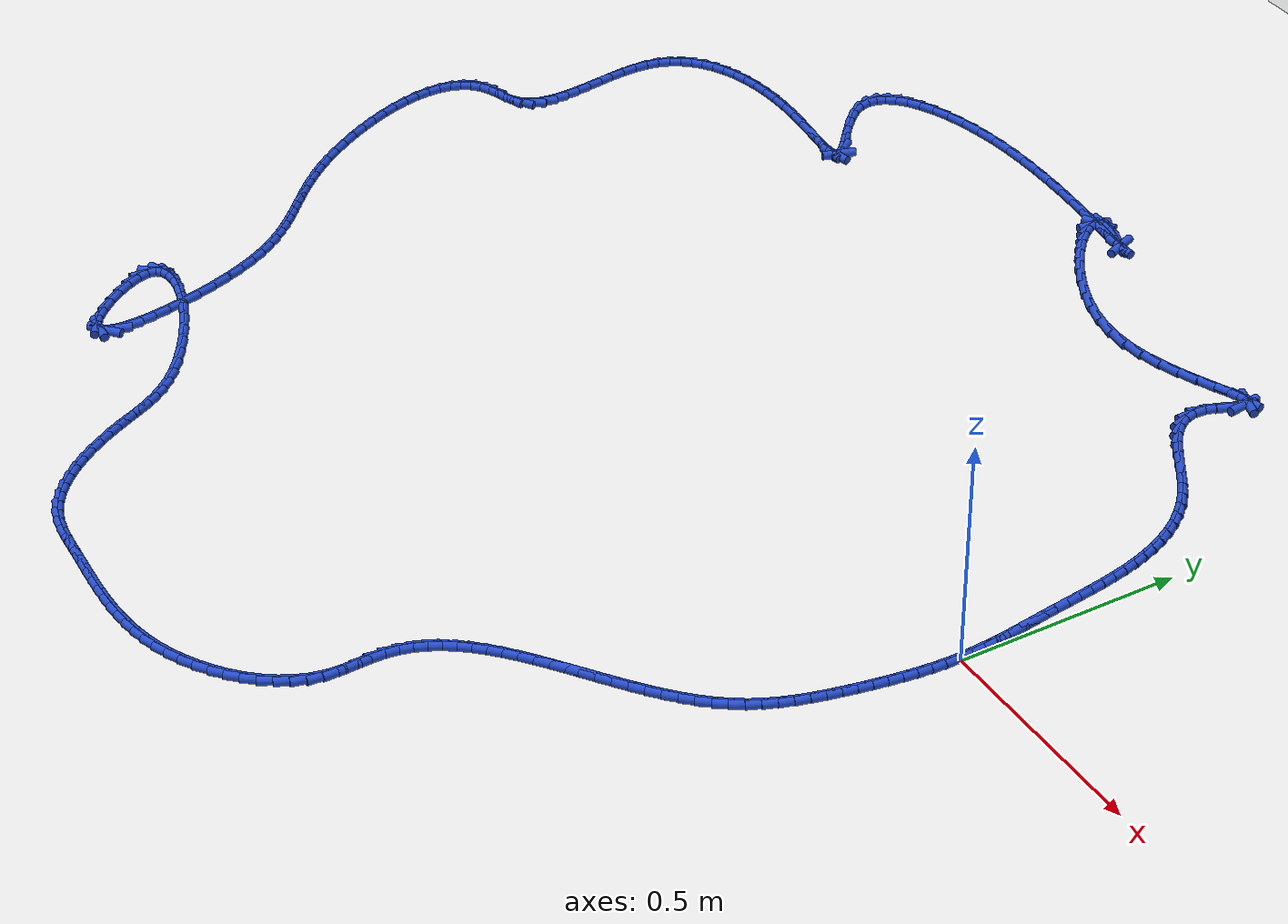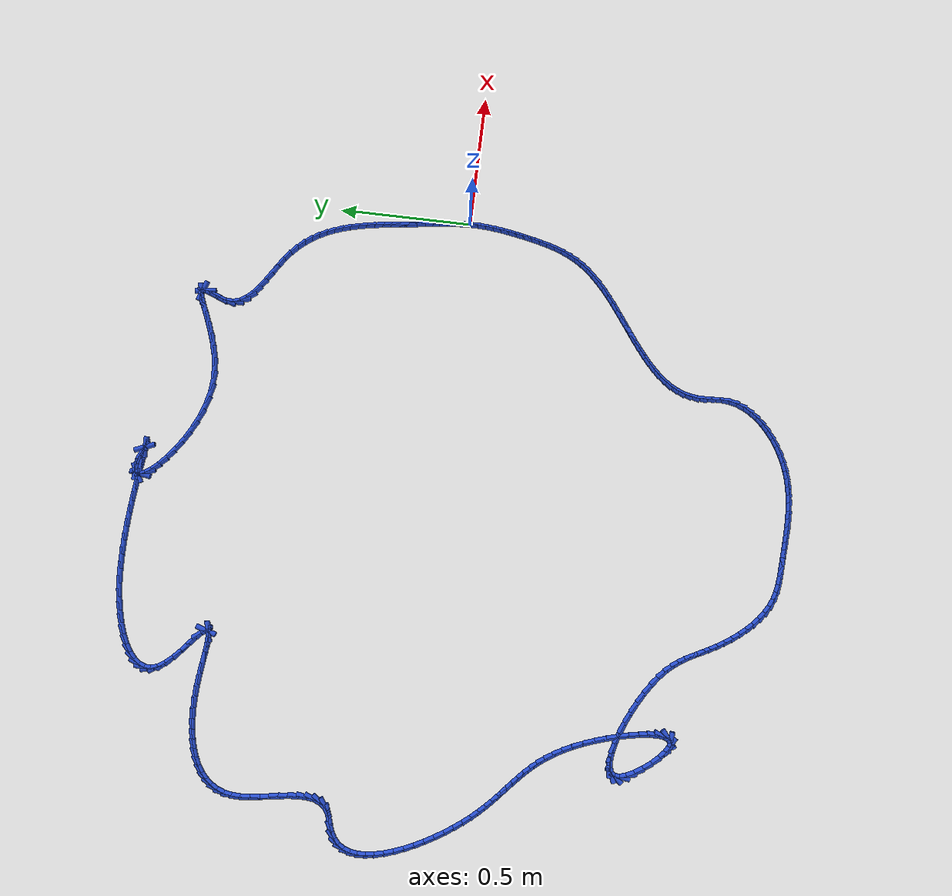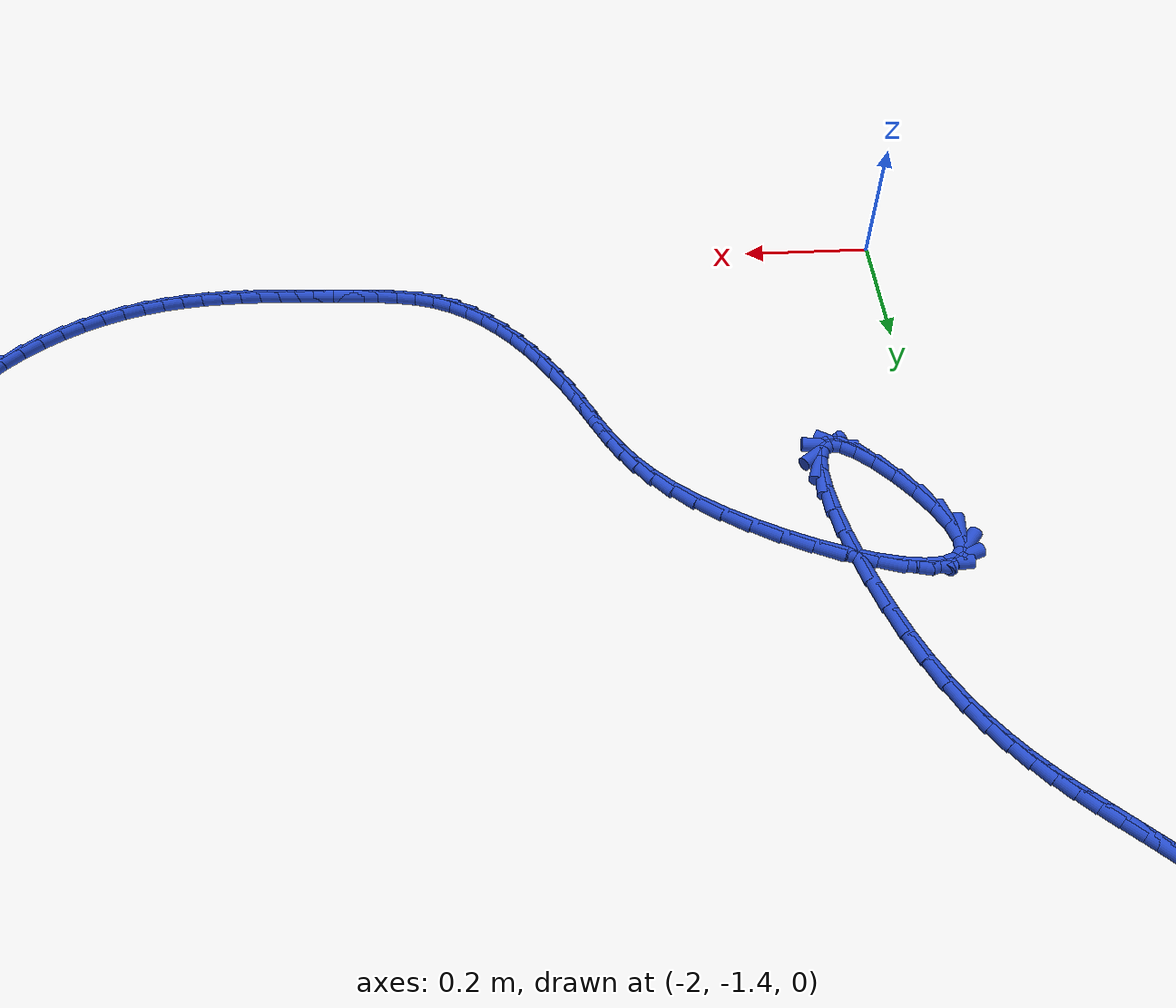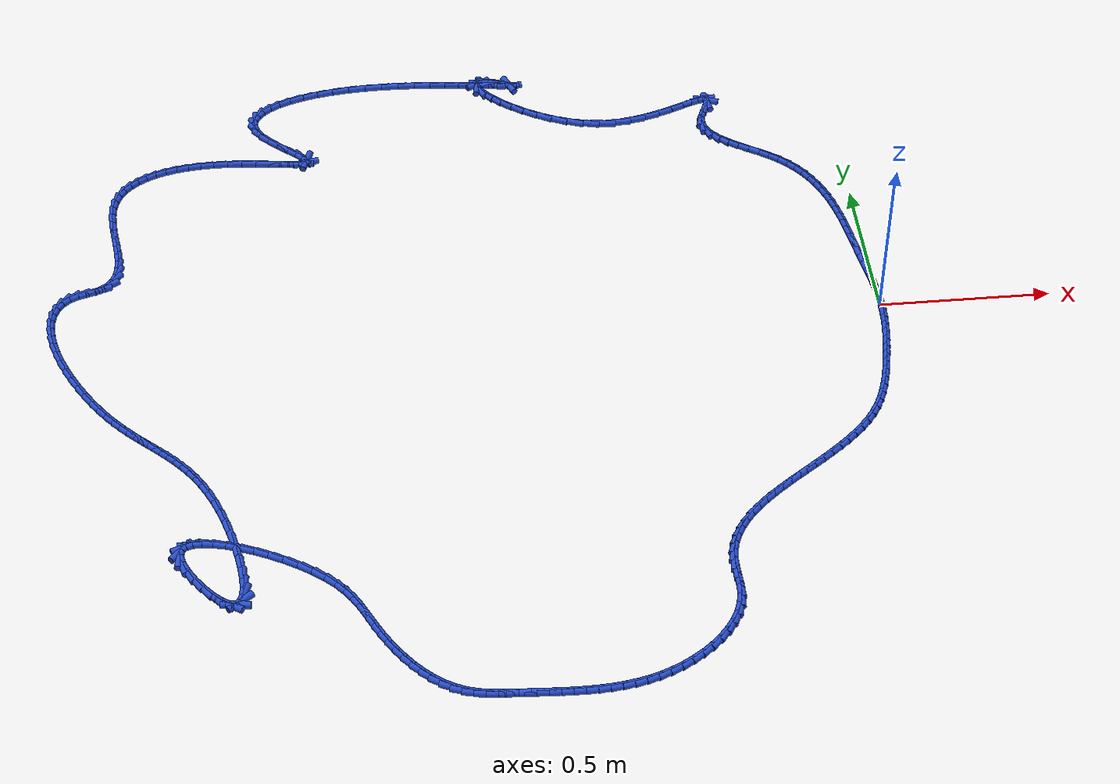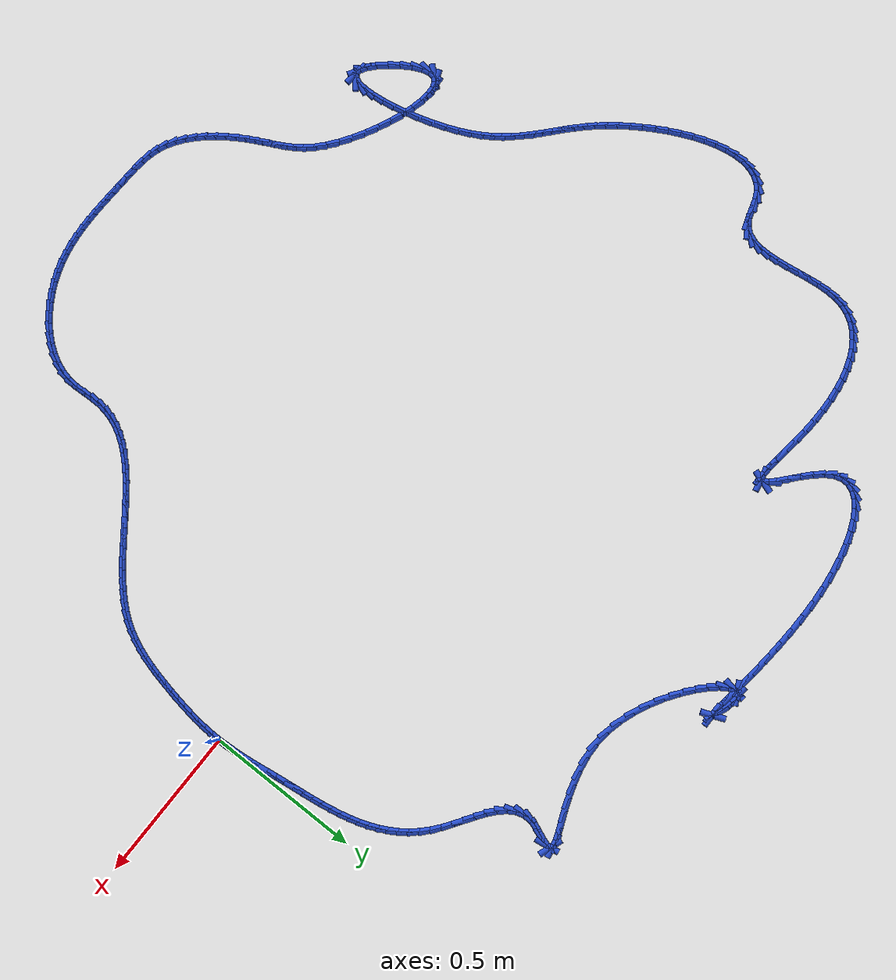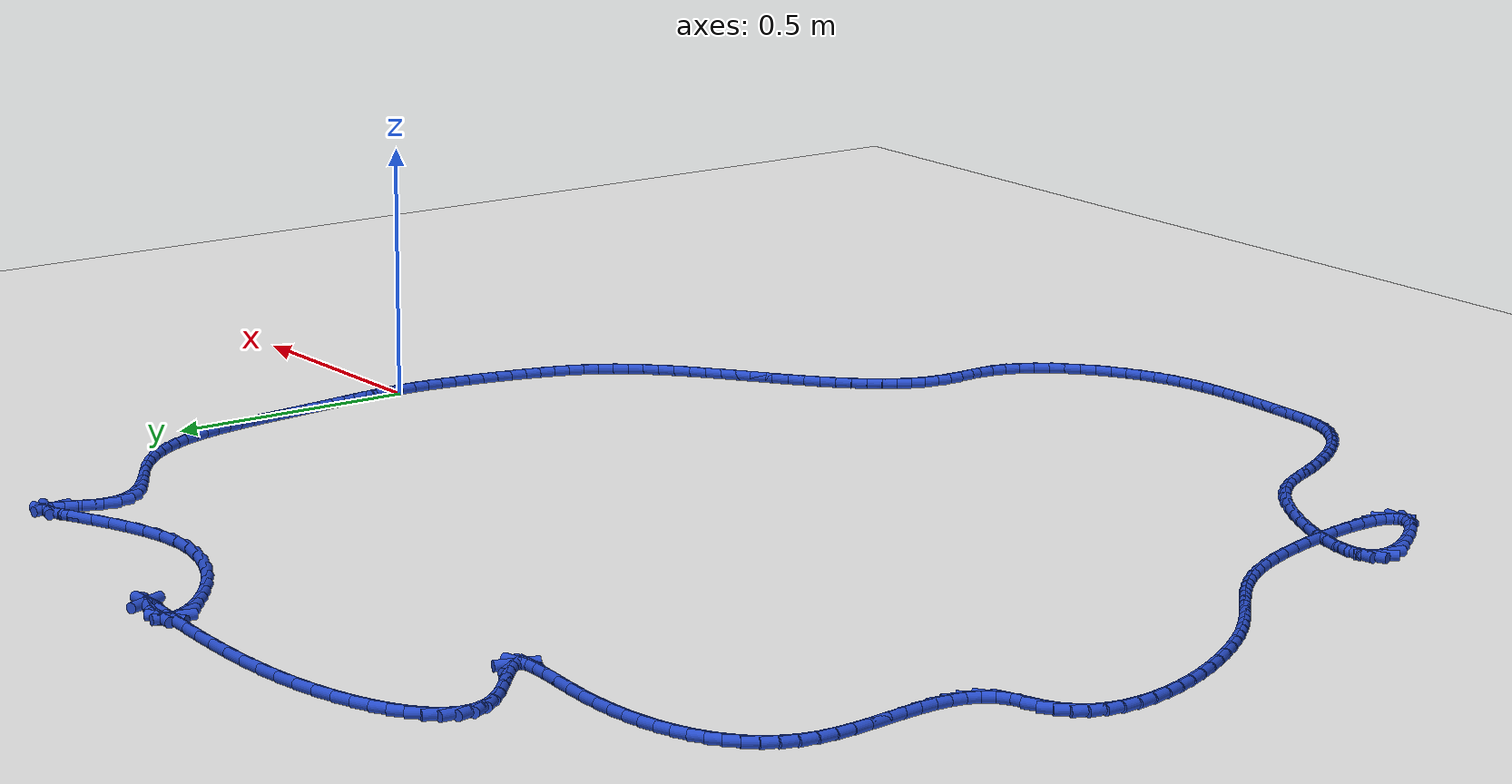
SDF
<sdf version="1.6">
 <world name="default">
  <light name="sun" type="directional">
   <pose>0 0 10 0 -0 0</pose>
   <diffuse>0.8 0.8 0.8 1</diffuse>
   <specular>0.2 0.2 0.2 1</specular>
   <attenuation>
    <range>1000</range>
    <constant>0.9</constant>
    <linear>0.01</linear>
    <quadratic>0.001</quadratic>
   </attenuation>
   <direction>-0.5 0.1 -0.9</direction>
  </light>
  <model name="ground_plane">
   <static>1</static>
   <link name="link">
    <collision name="collision">
     <geometry><plane><normal>0 0 1</normal><size>100 100</size></plane></geometry>
     <surface><friction><ode><mu>100</mu><mu2>50</mu2></ode></friction></surface>
    </collision>
    <visual name="visual">
     <cast_shadows>0</cast_shadows>
     <geometry><plane><normal>0 0 1</normal><size>100 100</size></plane></geometry>
     <material>
      <script><uri>file://media/materials/scripts/gazebo.material</uri><name>Gazebo/WhiteGlow</name></script>
     </material>
    </visual>
   </link>
  </model>
  <gravity>0 0 -9.8</gravity>
  <magnetic_field>6e-06 2.3e-05 -4.2e-05</magnetic_field>
  <atmosphere type="adiabatic"/>
  <physics name="default_physics" default="0" type="ode">
   <max_step_size>0.001</max_step_size>
   <real_time_factor>1</real_time_factor>
   <real_time_update_rate>1000</real_time_update_rate>
  </physics>
  <scene><ambient>0.4 0.4 0.4 1</ambient><background>0.7 0.7 0.7 1</background><shadows>1</shadows></scene>
  <spherical_coordinates>
   <surface_model>EARTH_WGS84</surface_model>
   <latitude_deg>0</latitude_deg>
   <longitude_deg>0</longitude_deg>
   <elevation>0</elevation>
   <heading_deg>0</heading_deg>
  </spherical_coordinates>
  <model name="line">
   <link name="link_0">
    <pose>2.6020852139652106e-18 -6.938893903907228e-18 0.01 0 1.57 -1.535119810844154</pose>
    <collision name="collision">
     <geometry><cylinder><radius>0.01</radius><length>0.08</length></cylinder></geometry>
    </collision>
    <visual name="visual">
     <material>
      <script><name>Gazebo/Blue</name><uri>file://media/materials/scripts/gazebo.material</uri></script>
     </material>
     <geometry><cylinder><radius>0.01</radius><length>0.08</length></cylinder></geometry>
    </visual>
   </link>
   <link name="link_1">
    <pose>-0.0010793961114417964 0.030242250036836178 0.01 0 1.57 -1.4972439240679134</pose>
    <collision name="collision">
     <geometry><cylinder><radius>0.01</radius><length>0.08</length></cylinder></geometry>
    </collision>
    <visual name="visual">
     <material>
      <script><name>Gazebo/Blue</name><uri>file://media/materials/scripts/gazebo.material</uri></script>
     </material>
     <geometry><cylinder><radius>0.01</radius><length>0.08</length></cylinder></geometry>
    </visual>
   </link>
   <link name="link_2">
    <pose>-0.0033058834710195336 0.0604584056234154 0.01 0 1.57 -1.4671298274070912</pose>
    <collision name="collision">
     <geometry><cylinder><radius>0.01</radius><length>0.08</length></cylinder></geometry>
    </collision>
    <visual name="visual">
     <material>
      <script><name>Gazebo/Blue</name><uri>file://media/materials/scripts/gazebo.material</uri></script>
     </material>
     <geometry><cylinder><radius>0.01</radius><length>0.08</length></cylinder></geometry>
    </visual>
   </link>
   <link name="link_3">
    <pose>-0.006451480284367642 0.09069305658074162 0.01 0 1.57 -1.4448327646201642</pose>
    <collision name="collision">
     <geometry><cylinder><radius>0.01</radius><length>0.08</length></cylinder></geometry>
    </collision>
    <visual name="visual">
     <material>
      <script><name>Gazebo/Blue</name><uri>file://media/materials/scripts/gazebo.material</uri></script>
     </material>
     <geometry><cylinder><radius>0.01</radius><length>0.08</length></cylinder></geometry>
    </visual>
   </link>
   <link name="link_4">
    <pose>-0.010288204757120561 0.12099079272981879 0.01 0 1.57 -1.430309983116135</pose>
    <collision name="collision">
     <geometry><cylinder><radius>0.01</radius><length>0.08</length></cylinder></geometry>
    </collision>
    <visual name="visual">
     <material>
      <script><name>Gazebo/Blue</name><uri>file://media/materials/scripts/gazebo.material</uri></script>
     </material>
     <geometry><cylinder><radius>0.01</radius><length>0.08</length></cylinder></geometry>
    </visual>
   </link>
   <link name="link_5">
    <pose>-0.014588075094912717 0.15139620389165087 0.01 0 1.57 -1.4234627227017236</pose>
    <collision name="collision">
     <geometry><cylinder><radius>0.01</radius><length>0.08</length></cylinder></geometry>
    </collision>
    <visual name="visual">
     <material>
      <script><name>Gazebo/Blue</name><uri>file://media/materials/scripts/gazebo.material</uri></script>
     </material>
     <geometry><cylinder><radius>0.01</radius><length>0.08</length></cylinder></geometry>
    </visual>
   </link>
   <link name="link_6">
    <pose>-0.019123109503378553 0.18195387988724185 0.01 0 1.57 -1.4241637624771013</pose>
    <collision name="collision">
     <geometry><cylinder><radius>0.01</radius><length>0.08</length></cylinder></geometry>
    </collision>
    <visual name="visual">
     <material>
      <script><name>Gazebo/Blue</name><uri>file://media/materials/scripts/gazebo.material</uri></script>
     </material>
     <geometry><cylinder><radius>0.01</radius><length>0.08</length></cylinder></geometry>
    </visual>
   </link>
   <link name="link_7">
    <pose>-0.023665326188152494 0.21270841053759562 0.01 0 1.57 -1.4315012945426484</pose>
    <collision name="collision">
     <geometry><cylinder><radius>0.01</radius><length>0.08</length></cylinder></geometry>
    </collision>
    <visual name="visual">
     <material>
      <script><name>Gazebo/Blue</name><uri>file://media/materials/scripts/gazebo.material</uri></script>
     </material>
     <geometry><cylinder><radius>0.01</radius><length>0.08</length></cylinder></geometry>
    </visual>
   </link>
   <link name="link_8">
    <pose>-0.028009952000439854 0.24369651960343938 0.01 0 1.57 -1.4369575729298536</pose>
    <collision name="collision">
     <geometry><cylinder><radius>0.01</radius><length>0.08</length></cylinder></geometry>
    </collision>
    <visual name="visual">
     <material>
      <script><name>Gazebo/Blue</name><uri>file://media/materials/scripts/gazebo.material</uri></script>
     </material>
     <geometry><cylinder><radius>0.01</radius><length>0.08</length></cylinder></geometry>
    </visual>
   </link>
   <link name="link_9">
    <pose>-0.03220706884932136 0.2748685533254936 0.01 0 1.57 -1.4354091824036643</pose>
    <collision name="collision">
     <geometry><cylinder><radius>0.01</radius><length>0.08</length></cylinder></geometry>
    </collision>
    <visual name="visual">
     <material>
      <script><name>Gazebo/Blue</name><uri>file://media/materials/scripts/gazebo.material</uri></script>
     </material>
     <geometry><cylinder><radius>0.01</radius><length>0.08</length></cylinder></geometry>
    </visual>
   </link>
   <link name="link_10">
    <pose>-0.03646435201114002 0.3061214451366384 0.01 0 1.57 -1.4268272968068414</pose>
    <collision name="collision">
     <geometry><cylinder><radius>0.01</radius><length>0.08</length></cylinder></geometry>
    </collision>
    <visual name="visual">
     <material>
      <script><name>Gazebo/Blue</name><uri>file://media/materials/scripts/gazebo.material</uri></script>
     </material>
     <geometry><cylinder><radius>0.01</radius><length>0.08</length></cylinder></geometry>
    </visual>
   </link>
   <link name="link_11">
    <pose>-0.04099181286505175 0.33735133669905387 0.01 0 1.57 -1.41116424702753</pose>
    <collision name="collision">
     <geometry><cylinder><radius>0.01</radius><length>0.08</length></cylinder></geometry>
    </collision>
    <visual name="visual">
     <material>
      <script><name>Gazebo/Blue</name><uri>file://media/materials/scripts/gazebo.material</uri></script>
     </material>
     <geometry><cylinder><radius>0.01</radius><length>0.08</length></cylinder></geometry>
    </visual>
   </link>
   <link name="link_12">
    <pose>-0.045999462790212504 0.3684543696749204 0.01 0 1.57 -1.3882882878004281</pose>
    <collision name="collision">
     <geometry><cylinder><radius>0.01</radius><length>0.08</length></cylinder></geometry>
    </collision>
    <visual name="visual">
     <material>
      <script><name>Gazebo/Blue</name><uri>file://media/materials/scripts/gazebo.material</uri></script>
     </material>
     <geometry><cylinder><radius>0.01</radius><length>0.08</length></cylinder></geometry>
    </visual>
   </link>
   <link name="link_13">
    <pose>-0.05169731316577824 0.3993266857264182 0.01 0 1.57 -1.3580047832749678</pose>
    <collision name="collision">
     <geometry><cylinder><radius>0.01</radius><length>0.08</length></cylinder></geometry>
    </collision>
    <visual name="visual">
     <material>
      <script><name>Gazebo/Blue</name><uri>file://media/materials/scripts/gazebo.material</uri></script>
     </material>
     <geometry><cylinder><radius>0.01</radius><length>0.08</length></cylinder></geometry>
    </visual>
   </link>
   <link name="link_14">
    <pose>-0.058295375370904894 0.4298644265157277 0.01 0 1.57 -1.320089366613279</pose>
    <collision name="collision">
     <geometry><cylinder><radius>0.01</radius><length>0.08</length></cylinder></geometry>
    </collision>
    <visual name="visual">
     <material>
      <script><name>Gazebo/Blue</name><uri>file://media/materials/scripts/gazebo.material</uri></script>
     </material>
     <geometry><cylinder><radius>0.01</radius><length>0.08</length></cylinder></geometry>
    </visual>
   </link>
   <link name="link_15">
    <pose>-0.06600366078474841 0.459963733705029 0.01 0 1.57 -1.2743368600120932</pose>
    <collision name="collision">
     <geometry><cylinder><radius>0.01</radius><length>0.08</length></cylinder></geometry>
    </collision>
    <visual name="visual">
     <material>
      <script><name>Gazebo/Blue</name><uri>file://media/materials/scripts/gazebo.material</uri></script>
     </material>
     <geometry><cylinder><radius>0.01</radius><length>0.08</length></cylinder></geometry>
    </visual>
   </link>
   <link name="link_16">
    <pose>-0.07503218078646476 0.48952074895650255 0.01 0 1.57 -1.2206291843248722</pose>
    <collision name="collision">
     <geometry><cylinder><radius>0.01</radius><length>0.08</length></cylinder></geometry>
    </collision>
    <visual name="visual">
     <material>
      <script><name>Gazebo/Blue</name><uri>file://media/materials/scripts/gazebo.material</uri></script>
     </material>
     <geometry><cylinder><radius>0.01</radius><length>0.08</length></cylinder></geometry>
    </visual>
   </link>
   <link name="link_17">
    <pose>-0.08559094675520985 0.5184316139323285 0.01 0 1.57 -1.1590224466731098</pose>
    <collision name="collision">
     <geometry><cylinder><radius>0.01</radius><length>0.08</length></cylinder></geometry>
    </collision>
    <visual name="visual">
     <material>
      <script><name>Gazebo/Blue</name><uri>file://media/materials/scripts/gazebo.material</uri></script>
     </material>
     <geometry><cylinder><radius>0.01</radius><length>0.08</length></cylinder></geometry>
    </visual>
   </link>
   <link name="link_18">
    <pose>-0.09788997007013965 0.5465924702946873 0.01 0 1.57 -1.0898466677093053</pose>
    <collision name="collision">
     <geometry><cylinder><radius>0.01</radius><length>0.08</length></cylinder></geometry>
    </collision>
    <visual name="visual">
     <material>
      <script><name>Gazebo/Blue</name><uri>file://media/materials/scripts/gazebo.material</uri></script>
     </material>
     <geometry><cylinder><radius>0.01</radius><length>0.08</length></cylinder></geometry>
    </visual>
   </link>
   <link name="link_19">
    <pose>-0.11213926211041013 0.5738994597057592 0.01 0 1.57 -1.013801095192671</pose>
    <collision name="collision">
     <geometry><cylinder><radius>0.01</radius><length>0.08</length></cylinder></geometry>
    </collision>
    <visual name="visual">
     <material>
      <script><name>Gazebo/Blue</name><uri>file://media/materials/scripts/gazebo.material</uri></script>
     </material>
     <geometry><cylinder><radius>0.01</radius><length>0.08</length></cylinder></geometry>
    </visual>
   </link>
   <link name="link_20">
    <pose>-0.1285488342551772 0.6002487238277243 0.01 0 1.57 -0.9320166604354299</pose>
    <collision name="collision">
     <geometry><cylinder><radius>0.01</radius><length>0.08</length></cylinder></geometry>
    </collision>
    <visual name="visual">
     <material>
      <script><name>Gazebo/Blue</name><uri>file://media/materials/scripts/gazebo.material</uri></script>
     </material>
     <geometry><cylinder><radius>0.01</radius><length>0.08</length></cylinder></geometry>
    </visual>
   </link>
   <link name="link_21">
    <pose>-0.14732869788359682 0.625536404322763 0.01 0 1.57 -0.8460520378949752</pose>
    <collision name="collision">
     <geometry><cylinder><radius>0.01</radius><length>0.08</length></cylinder></geometry>
    </collision>
    <visual name="visual">
     <material>
      <script><name>Gazebo/Blue</name><uri>file://media/materials/scripts/gazebo.material</uri></script>
     </material>
     <geometry><cylinder><radius>0.01</radius><length>0.08</length></cylinder></geometry>
    </visual>
   </link>
   <link name="link_22">
    <pose>-0.16868886437482494 0.6496586428530557 0.01 0 1.57 -0.7577998931712115</pose>
    <collision name="collision">
     <geometry><cylinder><radius>0.01</radius><length>0.08</length></cylinder></geometry>
    </collision>
    <visual name="visual">
     <material>
      <script><name>Gazebo/Blue</name><uri>file://media/materials/scripts/gazebo.material</uri></script>
     </material>
     <geometry><cylinder><radius>0.01</radius><length>0.08</length></cylinder></geometry>
    </visual>
   </link>
   <link name="link_23">
    <pose>-0.19283934510801748 0.6725115810807826 0.01 0 1.57 -0.6706661141050235</pose>
    <collision name="collision">
     <geometry><cylinder><radius>0.01</radius><length>0.08</length></cylinder></geometry>
    </collision>
    <visual name="visual">
     <material>
      <script><name>Gazebo/Blue</name><uri>file://media/materials/scripts/gazebo.material</uri></script>
     </material>
     <geometry><cylinder><radius>0.01</radius><length>0.08</length></cylinder></geometry>
    </visual>
   </link>
   <link name="link_24">
    <pose>-0.2199390092678758 0.6940108004372118 0.01 0 1.57 -0.6062227403508732</pose>
    <collision name="collision">
     <geometry><cylinder><radius>0.01</radius><length>0.08</length></cylinder></geometry>
    </collision>
    <visual name="visual">
     <material>
      <script><name>Gazebo/Blue</name><uri>file://media/materials/scripts/gazebo.material</uri></script>
     </material>
     <geometry><cylinder><radius>0.01</radius><length>0.08</length></cylinder></geometry>
    </visual>
   </link>
   <link name="link_25">
    <pose>-0.2493248066144553 0.7143843039067745 0.01 0 1.57 -0.5764447515231088</pose>
    <collision name="collision">
     <geometry><cylinder><radius>0.01</radius><length>0.08</length></cylinder></geometry>
    </collision>
    <visual name="visual">
     <material>
      <script><name>Gazebo/Blue</name><uri>file://media/materials/scripts/gazebo.material</uri></script>
     </material>
     <geometry><cylinder><radius>0.01</radius><length>0.08</length></cylinder></geometry>
    </visual>
   </link>
   <link name="link_26">
    <pose>-0.27967066860889955 0.7341121157797765 0.01 0 1.57 -0.5785941751113316</pose>
    <collision name="collision">
     <geometry><cylinder><radius>0.01</radius><length>0.08</length></cylinder></geometry>
    </collision>
    <visual name="visual">
     <material>
      <script><name>Gazebo/Blue</name><uri>file://media/materials/scripts/gazebo.material</uri></script>
     </material>
     <geometry><cylinder><radius>0.01</radius><length>0.08</length></cylinder></geometry>
    </visual>
   </link>
   <link name="link_27">
    <pose>-0.30963162527543586 0.7536814450121989 0.01 0 1.57 -0.6139588634260293</pose>
    <collision name="collision">
     <geometry><cylinder><radius>0.01</radius><length>0.08</length></cylinder></geometry>
    </collision>
    <visual name="visual">
     <material>
      <script><name>Gazebo/Blue</name><uri>file://media/materials/scripts/gazebo.material</uri></script>
     </material>
     <geometry><cylinder><radius>0.01</radius><length>0.08</length></cylinder></geometry>
    </visual>
   </link>
   <link name="link_28">
    <pose>-0.3378627066382919 0.7735795005600232 0.01 0 1.57 -0.6888554672768857</pose>
    <collision name="collision">
     <geometry><cylinder><radius>0.01</radius><length>0.08</length></cylinder></geometry>
    </collision>
    <visual name="visual">
     <material>
      <script><name>Gazebo/Blue</name><uri>file://media/materials/scripts/gazebo.material</uri></script>
     </material>
     <geometry><cylinder><radius>0.01</radius><length>0.08</length></cylinder></geometry>
    </visual>
   </link>
   <link name="link_29">
    <pose>-0.36301894272169405 0.7942934913792294 0.01 0 1.57 -0.815344943659757</pose>
    <collision name="collision">
     <geometry><cylinder><radius>0.01</radius><length>0.08</length></cylinder></geometry>
    </collision>
    <visual name="visual">
     <material>
      <script><name>Gazebo/Blue</name><uri>file://media/materials/scripts/gazebo.material</uri></script>
     </material>
     <geometry><cylinder><radius>0.01</radius><length>0.08</length></cylinder></geometry>
    </visual>
   </link>
   <link name="link_30">
    <pose>-0.3837553635498704 0.8163106264258 0.01 0 1.57 -1.0094243329663657</pose>
    <collision name="collision">
     <geometry><cylinder><radius>0.01</radius><length>0.08</length></cylinder></geometry>
    </collision>
    <visual name="visual">
     <material>
      <script><name>Gazebo/Blue</name><uri>file://media/materials/scripts/gazebo.material</uri></script>
     </material>
     <geometry><cylinder><radius>0.01</radius><length>0.08</length></cylinder></geometry>
    </visual>
   </link>
   <link name="link_31">
    <pose>-0.3987269991470475 0.8401181146557147 0.01 0 1.57 -1.2780610288470609</pose>
    <collision name="collision">
     <geometry><cylinder><radius>0.01</radius><length>0.08</length></cylinder></geometry>
    </collision>
    <visual name="visual">
     <material>
      <script><name>Gazebo/Blue</name><uri>file://media/materials/scripts/gazebo.material</uri></script>
     </material>
     <geometry><cylinder><radius>0.01</radius><length>0.08</length></cylinder></geometry>
    </visual>
   </link>
   <link name="link_32">
    <pose>-0.40658887953745293 0.8662031650249556 0.01 0 1.57 1.550249878488988</pose>
    <collision name="collision">
     <geometry><cylinder><radius>0.01</radius><length>0.08</length></cylinder></geometry>
    </collision>
    <visual name="visual">
     <material>
      <script><name>Gazebo/Blue</name><uri>file://media/materials/scripts/gazebo.material</uri></script>
     </material>
     <geometry><cylinder><radius>0.01</radius><length>0.08</length></cylinder></geometry>
    </visual>
   </link>
   <link name="link_33">
    <pose>-0.4059960347453139 0.8950529864895036 0.01 0 1.57 1.2862029149961807</pose>
    <collision name="collision">
     <geometry><cylinder><radius>0.01</radius><length>0.08</length></cylinder></geometry>
    </collision>
    <visual name="visual">
     <material>
      <script><name>Gazebo/Blue</name><uri>file://media/materials/scripts/gazebo.material</uri></script>
     </material>
     <geometry><cylinder><radius>0.01</radius><length>0.08</length></cylinder></geometry>
    </visual>
   </link>
   <link name="link_34">
    <pose>-0.396853515012452 0.926305813460769 0.01 0 1.57 1.1871699023313167</pose>
    <collision name="collision">
     <geometry><cylinder><radius>0.01</radius><length>0.08</length></cylinder></geometry>
    </collision>
    <visual name="visual">
     <material>
      <script><name>Gazebo/Blue</name><uri>file://media/materials/scripts/gazebo.material</uri></script>
     </material>
     <geometry><cylinder><radius>0.01</radius><length>0.08</length></cylinder></geometry>
    </visual>
   </link>
   <link name="link_35">
    <pose>-0.3850576069627497 0.9555308204203452 0.01 0 1.57 1.2628143666298952</pose>
    <collision name="collision">
     <geometry><cylinder><radius>0.01</radius><length>0.08</length></cylinder></geometry>
    </collision>
    <visual name="visual">
     <material>
      <script><name>Gazebo/Blue</name><uri>file://media/materials/scripts/gazebo.material</uri></script>
     </material>
     <geometry><cylinder><radius>0.01</radius><length>0.08</length></cylinder></geometry>
    </visual>
   </link>
   <link name="link_36">
    <pose>-0.37816752769008594 0.9771906642832503 0.01 0 1.57 -1.4206220915391952</pose>
    <collision name="collision">
     <geometry><cylinder><radius>0.01</radius><length>0.08</length></cylinder></geometry>
    </collision>
    <visual name="visual">
     <material>
      <script><name>Gazebo/Blue</name><uri>file://media/materials/scripts/gazebo.material</uri></script>
     </material>
     <geometry><cylinder><radius>0.01</radius><length>0.08</length></cylinder></geometry>
    </visual>
   </link>
   <link name="link_37">
    <pose>-0.3799528780520467 0.988989684827292 0.01 0 1.57 -0.3224654441758275</pose>
    <collision name="collision">
     <geometry><cylinder><radius>0.01</radius><length>0.08</length></cylinder></geometry>
    </collision>
    <visual name="visual">
     <material>
      <script><name>Gazebo/Blue</name><uri>file://media/materials/scripts/gazebo.material</uri></script>
     </material>
     <geometry><cylinder><radius>0.01</radius><length>0.08</length></cylinder></geometry>
    </visual>
   </link>
   <link name="link_38">
    <pose>-0.3898855505117467 0.9923084672691068 0.01 0 1.57 0.20396368487632466</pose>
    <collision name="collision">
     <geometry><cylinder><radius>0.01</radius><length>0.08</length></cylinder></geometry>
    </collision>
    <visual name="visual">
     <material>
      <script><name>Gazebo/Blue</name><uri>file://media/materials/scripts/gazebo.material</uri></script>
     </material>
     <geometry><cylinder><radius>0.01</radius><length>0.08</length></cylinder></geometry>
    </visual>
   </link>
   <link name="link_39">
    <pose>-0.40720547740940005 0.9887260147414699 0.01 0 1.57 0.3560043414878191</pose>
    <collision name="collision">
     <geometry><cylinder><radius>0.01</radius><length>0.08</length></cylinder></geometry>
    </collision>
    <visual name="visual">
     <material>
      <script><name>Gazebo/Blue</name><uri>file://media/materials/scripts/gazebo.material</uri></script>
     </material>
     <geometry><cylinder><radius>0.01</radius><length>0.08</length></cylinder></geometry>
    </visual>
   </link>
   <link name="link_40">
    <pose>-0.43115259108522064 0.9798213303771566 0.01 0 1.57 0.4012131841923045</pose>
    <collision name="collision">
     <geometry><cylinder><radius>0.01</radius><length>0.08</length></cylinder></geometry>
    </collision>
    <visual name="visual">
     <material>
      <script><name>Gazebo/Blue</name><uri>file://media/materials/scripts/gazebo.material</uri></script>
     </material>
     <geometry><cylinder><radius>0.01</radius><length>0.08</length></cylinder></geometry>
    </visual>
   </link>
   <link name="link_41">
    <pose>-0.4609668238794226 0.9671734173089418 0.01 0 1.57 0.40115716610041635</pose>
    <collision name="collision">
     <geometry><cylinder><radius>0.01</radius><length>0.08</length></cylinder></geometry>
    </collision>
    <visual name="visual">
     <material>
      <script><name>Gazebo/Blue</name><uri>file://media/materials/scripts/gazebo.material</uri></script>
     </material>
     <geometry><cylinder><radius>0.01</radius><length>0.08</length></cylinder></geometry>
    </visual>
   </link>
   <link name="link_42">
    <pose>-0.4958881081322197 0.9523612786696009 0.01 0 1.57 0.37368356504472544</pose>
    <collision name="collision">
     <geometry><cylinder><radius>0.01</radius><length>0.08</length></cylinder></geometry>
    </collision>
    <visual name="visual">
     <material>
      <script><name>Gazebo/Blue</name><uri>file://media/materials/scripts/gazebo.material</uri></script>
     </material>
     <geometry><cylinder><radius>0.01</radius><length>0.08</length></cylinder></geometry>
    </visual>
   </link>
   <link name="link_43">
    <pose>-0.5351563761838262 0.9369639175919092 0.01 0 1.57 0.32423749838795846</pose>
    <collision name="collision">
     <geometry><cylinder><radius>0.01</radius><length>0.08</length></cylinder></geometry>
    </collision>
    <visual name="visual">
     <material>
      <script><name>Gazebo/Blue</name><uri>file://media/materials/scripts/gazebo.material</uri></script>
     </material>
     <geometry><cylinder><radius>0.01</radius><length>0.08</length></cylinder></geometry>
    </visual>
   </link>
   <link name="link_44">
    <pose>-0.5780115603744562 0.9225603372086413 0.01 0 1.57 0.2534137149376096</pose>
    <collision name="collision">
     <geometry><cylinder><radius>0.01</radius><length>0.08</length></cylinder></geometry>
    </collision>
    <visual name="visual">
     <material>
      <script><name>Gazebo/Blue</name><uri>file://media/materials/scripts/gazebo.material</uri></script>
     </material>
     <geometry><cylinder><radius>0.01</radius><length>0.08</length></cylinder></geometry>
    </visual>
   </link>
   <link name="link_45">
    <pose>-0.6236935930443233 0.9107295406525732 0.01 0 1.57 0.15945561878747366</pose>
    <collision name="collision">
     <geometry><cylinder><radius>0.01</radius><length>0.08</length></cylinder></geometry>
    </collision>
    <visual name="visual">
     <material>
      <script><name>Gazebo/Blue</name><uri>file://media/materials/scripts/gazebo.material</uri></script>
     </material>
     <geometry><cylinder><radius>0.01</radius><length>0.08</length></cylinder></geometry>
    </visual>
   </link>
   <link name="link_46">
    <pose>-0.6714424065336424 0.9030505310564794 0.01 0 1.57 0.03969371709392719</pose>
    <collision name="collision">
     <geometry><cylinder><radius>0.01</radius><length>0.08</length></cylinder></geometry>
    </collision>
    <visual name="visual">
     <material>
      <script><name>Gazebo/Blue</name><uri>file://media/materials/scripts/gazebo.material</uri></script>
     </material>
     <geometry><cylinder><radius>0.01</radius><length>0.08</length></cylinder></geometry>
    </visual>
   </link>
   <link name="link_47">
    <pose>-0.7204979331826262 0.9011023115531354 0.01 0 1.57 -0.10300616908809843</pose>
    <collision name="collision">
     <geometry><cylinder><radius>0.01</radius><length>0.08</length></cylinder></geometry>
    </collision>
    <visual name="visual">
     <material>
      <script><name>Gazebo/Blue</name><uri>file://media/materials/scripts/gazebo.material</uri></script>
     </material>
     <geometry><cylinder><radius>0.01</radius><length>0.08</length></cylinder></geometry>
    </visual>
   </link>
   <link name="link_48">
    <pose>-0.7700902275220379 0.9062287676766682 0.01 0 1.57 -0.23494045824968374</pose>
    <collision name="collision">
     <geometry><cylinder><radius>0.01</radius><length>0.08</length></cylinder></geometry>
    </collision>
    <visual name="visual">
     <material>
      <script><name>Gazebo/Blue</name><uri>file://media/materials/scripts/gazebo.material</uri></script>
     </material>
     <geometry><cylinder><radius>0.01</radius><length>0.08</length></cylinder></geometry>
    </visual>
   </link>
   <link name="link_49">
    <pose>-0.8193759084340188 0.9180258252093576 0.01 0 1.57 -0.3448037854052913</pose>
    <collision name="collision">
     <geometry><cylinder><radius>0.01</radius><length>0.08</length></cylinder></geometry>
    </collision>
    <visual name="visual">
     <material>
      <script><name>Gazebo/Blue</name><uri>file://media/materials/scripts/gazebo.material</uri></script>
     </material>
     <geometry><cylinder><radius>0.01</radius><length>0.08</length></cylinder></geometry>
    </visual>
   </link>
   <link name="link_50">
    <pose>-0.8674785107365116 0.9353019230148576 0.01 0 1.57 -0.4379298929330122</pose>
    <collision name="collision">
     <geometry><cylinder><radius>0.01</radius><length>0.08</length></cylinder></geometry>
    </collision>
    <visual name="visual">
     <material>
      <script><name>Gazebo/Blue</name><uri>file://media/materials/scripts/gazebo.material</uri></script>
     </material>
     <geometry><cylinder><radius>0.01</radius><length>0.08</length></cylinder></geometry>
    </visual>
   </link>
   <link name="link_51">
    <pose>-0.9135214095128178 0.9568616978562421 0.01 0 1.57 -0.5194217289778663</pose>
    <collision name="collision">
     <geometry><cylinder><radius>0.01</radius><length>0.08</length></cylinder></geometry>
    </collision>
    <visual name="visual">
     <material>
      <script><name>Gazebo/Blue</name><uri>file://media/materials/scripts/gazebo.material</uri></script>
     </material>
     <geometry><cylinder><radius>0.01</radius><length>0.08</length></cylinder></geometry>
    </visual>
   </link>
   <link name="link_52">
    <pose>-0.9566279798462399 0.9815097864965862 0.01 0 1.57 -0.5940616421185152</pose>
    <collision name="collision">
     <geometry><cylinder><radius>0.01</radius><length>0.08</length></cylinder></geometry>
    </collision>
    <visual name="visual">
     <material>
      <script><name>Gazebo/Blue</name><uri>file://media/materials/scripts/gazebo.material</uri></script>
     </material>
     <geometry><cylinder><radius>0.01</radius><length>0.08</length></cylinder></geometry>
    </visual>
   </link>
   <link name="link_53">
    <pose>-0.9959215968200792 1.0080508256989646 0.01 0 1.57 -0.6668573409596705</pose>
    <collision name="collision">
     <geometry><cylinder><radius>0.01</radius><length>0.08</length></cylinder></geometry>
    </collision>
    <visual name="visual">
     <material>
      <script><name>Gazebo/Blue</name><uri>file://media/materials/scripts/gazebo.material</uri></script>
     </material>
     <geometry><cylinder><radius>0.01</radius><length>0.08</length></cylinder></geometry>
    </visual>
   </link>
   <link name="link_54">
    <pose>-1.030525635517638 1.0352894522264522 0.01 0 1.57 -0.7442410845214185</pose>
    <collision name="collision">
     <geometry><cylinder><radius>0.01</radius><length>0.08</length></cylinder></geometry>
    </collision>
    <visual name="visual">
     <material>
      <script><name>Gazebo/Blue</name><uri>file://media/materials/scripts/gazebo.material</uri></script>
     </material>
     <geometry><cylinder><radius>0.01</radius><length>0.08</length></cylinder></geometry>
    </visual>
   </link>
   <link name="link_55">
    <pose>-1.0595634710222186 1.0620303028421239 0.01 0 1.57 -0.8368339495621614</pose>
    <collision name="collision">
     <geometry><cylinder><radius>0.01</radius><length>0.08</length></cylinder></geometry>
    </collision>
    <visual name="visual">
     <material>
      <script><name>Gazebo/Blue</name><uri>file://media/materials/scripts/gazebo.material</uri></script>
     </material>
     <geometry><cylinder><radius>0.01</radius><length>0.08</length></cylinder></geometry>
    </visual>
   </link>
   <link name="link_56">
    <pose>-1.0821584784171225 1.087078014309054 0.01 0 1.57 -0.9672506630544655</pose>
    <collision name="collision">
     <geometry><cylinder><radius>0.01</radius><length>0.08</length></cylinder></geometry>
    </collision>
    <visual name="visual">
     <material>
      <script><name>Gazebo/Blue</name><uri>file://media/materials/scripts/gazebo.material</uri></script>
     </material>
     <geometry><cylinder><radius>0.01</radius><length>0.08</length></cylinder></geometry>
    </visual>
   </link>
   <link name="link_57">
    <pose>-1.0974340327856518 1.1092372233903176 0.01 0 1.57 -1.197496023455213</pose>
    <collision name="collision">
     <geometry><cylinder><radius>0.01</radius><length>0.08</length></cylinder></geometry>
    </collision>
    <visual name="visual">
     <material>
      <script><name>Gazebo/Blue</name><uri>file://media/materials/scripts/gazebo.material</uri></script>
     </material>
     <geometry><cylinder><radius>0.01</radius><length>0.08</length></cylinder></geometry>
    </visual>
   </link>
   <link name="link_58">
    <pose>-1.1045135092111087 1.1273125668489896 0.01 0 1.57 1.4162700365128498</pose>
    <collision name="collision">
     <geometry><cylinder><radius>0.01</radius><length>0.08</length></cylinder></geometry>
    </collision>
    <visual name="visual">
     <material>
      <script><name>Gazebo/Blue</name><uri>file://media/materials/scripts/gazebo.material</uri></script>
     </material>
     <geometry><cylinder><radius>0.01</radius><length>0.08</length></cylinder></geometry>
    </visual>
   </link>
   <link name="link_59">
    <pose>-1.102520282776795 1.1401086814481447 0.01 0 1.57 0.4868334210226846</pose>
    <collision name="collision">
     <geometry><cylinder><radius>0.01</radius><length>0.08</length></cylinder></geometry>
    </collision>
    <visual name="visual">
     <material>
      <script><name>Gazebo/Blue</name><uri>file://media/materials/scripts/gazebo.material</uri></script>
     </material>
     <geometry><cylinder><radius>0.01</radius><length>0.08</length></cylinder></geometry>
    </visual>
   </link>
   <link name="link_60">
    <pose>-1.0905777285660128 1.1464302039508572 0.01 0 1.57 -0.05906640362695847</pose>
    <collision name="collision">
     <geometry><cylinder><radius>0.01</radius><length>0.08</length></cylinder></geometry>
    </collision>
    <visual name="visual">
     <material>
      <script><name>Gazebo/Blue</name><uri>file://media/materials/scripts/gazebo.material</uri></script>
     </material>
     <geometry><cylinder><radius>0.01</radius><length>0.08</length></cylinder></geometry>
    </visual>
   </link>
   <link name="link_61">
    <pose>-1.067813456619347 1.145084034388114 0.01 0 1.57 -0.2565820646898393</pose>
    <collision name="collision">
     <geometry><cylinder><radius>0.01</radius><length>0.08</length></cylinder></geometry>
    </collision>
    <visual name="visual">
     <material>
      <script><name>Gazebo/Blue</name><uri>file://media/materials/scripts/gazebo.material</uri></script>
     </material>
     <geometry><cylinder><radius>0.01</radius><length>0.08</length></cylinder></geometry>
    </visual>
   </link>
   <link name="link_62">
    <pose>-1.0376419504355314 1.1371680860147368 0.01 0 1.57 -0.31182022867360376</pose>
    <collision name="collision">
     <geometry><cylinder><radius>0.01</radius><length>0.08</length></cylinder></geometry>
    </collision>
    <visual name="visual">
     <material>
      <script><name>Gazebo/Blue</name><uri>file://media/materials/scripts/gazebo.material</uri></script>
     </material>
     <geometry><cylinder><radius>0.01</radius><length>0.08</length></cylinder></geometry>
    </visual>
   </link>
   <link name="link_63">
    <pose>-1.0143641620968498 1.129664824281417 0.01 0 1.57 -0.38246307213703995</pose>
    <collision name="collision">
     <geometry><cylinder><radius>0.01</radius><length>0.08</length></cylinder></geometry>
    </collision>
    <visual name="visual">
     <material>
      <script><name>Gazebo/Blue</name><uri>file://media/materials/scripts/gazebo.material</uri></script>
     </material>
     <geometry><cylinder><radius>0.01</radius><length>0.08</length></cylinder></geometry>
    </visual>
   </link>
   <link name="link_64">
    <pose>-1.0027214514802136 1.1249812930701855 0.01 0 1.57 -1.176811339419271</pose>
    <collision name="collision">
     <geometry><cylinder><radius>0.01</radius><length>0.08</length></cylinder></geometry>
    </collision>
    <visual name="visual">
     <material>
      <script><name>Gazebo/Blue</name><uri>file://media/materials/scripts/gazebo.material</uri></script>
     </material>
     <geometry><cylinder><radius>0.01</radius><length>0.08</length></cylinder></geometry>
    </visual>
   </link>
   <link name="link_65">
    <pose>-1.0017967439737756 1.1227569461339122 0.01 0 1.57 0.016209609024027603</pose>
    <collision name="collision">
     <geometry><cylinder><radius>0.01</radius><length>0.08</length></cylinder></geometry>
    </collision>
    <visual name="visual">
     <material>
      <script><name>Gazebo/Blue</name><uri>file://media/materials/scripts/gazebo.material</uri></script>
     </material>
     <geometry><cylinder><radius>0.01</radius><length>0.08</length></cylinder></geometry>
    </visual>
   </link>
   <link name="link_66">
    <pose>-1.0106369802979063 1.1226136368076216 0.01 0 1.57 -0.08812213307603997</pose>
    <collision name="collision">
     <geometry><cylinder><radius>0.01</radius><length>0.08</length></cylinder></geometry>
    </collision>
    <visual name="visual">
     <material>
      <script><name>Gazebo/Blue</name><uri>file://media/materials/scripts/gazebo.material</uri></script>
     </material>
     <geometry><cylinder><radius>0.01</radius><length>0.08</length></cylinder></geometry>
    </visual>
   </link>
   <link name="link_67">
    <pose>-1.028289101172977 1.1241732184263387 0.01 0 1.57 -0.11258418655997683</pose>
    <collision name="collision">
     <geometry><cylinder><radius>0.01</radius><length>0.08</length></cylinder></geometry>
    </collision>
    <visual name="visual">
     <material>
      <script><name>Gazebo/Blue</name><uri>file://media/materials/scripts/gazebo.material</uri></script>
     </material>
     <geometry><cylinder><radius>0.01</radius><length>0.08</length></cylinder></geometry>
    </visual>
   </link>
   <link name="link_68">
    <pose>-1.0538000473193585 1.1270575443250888 0.01 0 1.57 -0.11763183637661032</pose>
    <collision name="collision">
     <geometry><cylinder><radius>0.01</radius><length>0.08</length></cylinder></geometry>
    </collision>
    <visual name="visual">
     <material>
      <script><name>Gazebo/Blue</name><uri>file://media/materials/scripts/gazebo.material</uri></script>
     </material>
     <geometry><cylinder><radius>0.01</radius><length>0.08</length></cylinder></geometry>
    </visual>
   </link>
   <link name="link_69">
    <pose>-1.0862167594574212 1.130888467838896 0.01 0 1.57 -0.11415982840350508</pose>
    <collision name="collision">
     <geometry><cylinder><radius>0.01</radius><length>0.08</length></cylinder></geometry>
    </collision>
    <visual name="visual">
     <material>
      <script><name>Gazebo/Blue</name><uri>file://media/materials/scripts/gazebo.material</uri></script>
     </material>
     <geometry><cylinder><radius>0.01</radius><length>0.08</length></cylinder></geometry>
    </visual>
   </link>
   <link name="link_70">
    <pose>-1.1245861783075373 1.1352878423027855 0.01 0 1.57 -0.10543595013639143</pose>
    <collision name="collision">
     <geometry><cylinder><radius>0.01</radius><length>0.08</length></cylinder></geometry>
    </collision>
    <visual name="visual">
     <material>
      <script><name>Gazebo/Blue</name><uri>file://media/materials/scripts/gazebo.material</uri></script>
     </material>
     <geometry><cylinder><radius>0.01</radius><length>0.08</length></cylinder></geometry>
    </visual>
   </link>
   <link name="link_71">
    <pose>-1.1679552445900767 1.1398775210517822 0.01 0 1.57 -0.09256976171266783</pose>
    <collision name="collision">
     <geometry><cylinder><radius>0.01</radius><length>0.08</length></cylinder></geometry>
    </collision>
    <visual name="visual">
     <material>
      <script><name>Gazebo/Blue</name><uri>file://media/materials/scripts/gazebo.material</uri></script>
     </material>
     <geometry><cylinder><radius>0.01</radius><length>0.08</length></cylinder></geometry>
    </visual>
   </link>
   <link name="link_72">
    <pose>-1.2153708990254108 1.144279357420911 0.01 0 1.57 -0.07579806615652541</pose>
    <collision name="collision">
     <geometry><cylinder><radius>0.01</radius><length>0.08</length></cylinder></geometry>
    </collision>
    <visual name="visual">
     <material>
      <script><name>Gazebo/Blue</name><uri>file://media/materials/scripts/gazebo.material</uri></script>
     </material>
     <geometry><cylinder><radius>0.01</radius><length>0.08</length></cylinder></geometry>
    </visual>
   </link>
   <link name="link_73">
    <pose>-1.2658800823339107 1.1481152047451961 0.01 0 1.57 -0.05486853162927027</pose>
    <collision name="collision">
     <geometry><cylinder><radius>0.01</radius><length>0.08</length></cylinder></geometry>
    </collision>
    <visual name="visual">
     <material>
      <script><name>Gazebo/Blue</name><uri>file://media/materials/scripts/gazebo.material</uri></script>
     </material>
     <geometry><cylinder><radius>0.01</radius><length>0.08</length></cylinder></geometry>
    </visual>
   </link>
   <link name="link_74">
    <pose>-1.3185297352359469 1.1510069163596635 0.01 0 1.57 -0.029143211040475025</pose>
    <collision name="collision">
     <geometry><cylinder><radius>0.01</radius><length>0.08</length></cylinder></geometry>
    </collision>
    <visual name="visual">
     <material>
      <script><name>Gazebo/Blue</name><uri>file://media/materials/scripts/gazebo.material</uri></script>
     </material>
     <geometry><cylinder><radius>0.01</radius><length>0.08</length></cylinder></geometry>
    </visual>
   </link>
   <link name="link_75">
    <pose>-1.37236679845189 1.152576345599337 0.01 0 1.57 0.0024227134727034345</pose>
    <collision name="collision">
     <geometry><cylinder><radius>0.01</radius><length>0.08</length></cylinder></geometry>
    </collision>
    <visual name="visual">
     <material>
      <script><name>Gazebo/Blue</name><uri>file://media/materials/scripts/gazebo.material</uri></script>
     </material>
     <geometry><cylinder><radius>0.01</radius><length>0.08</length></cylinder></geometry>
    </visual>
   </link>
   <link name="link_76">
    <pose>-1.4264382127021118 1.1524453457992418 0.01 0 1.57 0.041390844245382384</pose>
    <collision name="collision">
     <geometry><cylinder><radius>0.01</radius><length>0.08</length></cylinder></geometry>
    </collision>
    <visual name="visual">
     <material>
      <script><name>Gazebo/Blue</name><uri>file://media/materials/scripts/gazebo.material</uri></script>
     </material>
     <geometry><cylinder><radius>0.01</radius><length>0.08</length></cylinder></geometry>
    </visual>
   </link>
   <link name="link_77">
    <pose>-1.4797909187069824 1.1502357702944026 0.01 0 1.57 0.08905563460168993</pose>
    <collision name="collision">
     <geometry><cylinder><radius>0.01</radius><length>0.08</length></cylinder></geometry>
    </collision>
    <visual name="visual">
     <material>
      <script><name>Gazebo/Blue</name><uri>file://media/materials/scripts/gazebo.material</uri></script>
     </material>
     <geometry><cylinder><radius>0.01</radius><length>0.08</length></cylinder></geometry>
    </visual>
   </link>
   <link name="link_78">
    <pose>-1.531505501804089 1.1456180813334416 0.01 0 1.57 0.14162701321229326</pose>
    <collision name="collision">
     <geometry><cylinder><radius>0.01</radius><length>0.08</length></cylinder></geometry>
    </collision>
    <visual name="visual">
     <material>
      <script><name>Gazebo/Blue</name><uri>file://media/materials/scripts/gazebo.material</uri></script>
     </material>
     <geometry><cylinder><radius>0.01</radius><length>0.08</length></cylinder></geometry>
    </visual>
   </link>
   <link name="link_79">
    <pose>-1.5808808031648611 1.1385780718136183 0.01 0 1.57 0.19876933803984131</pose>
    <collision name="collision">
     <geometry><cylinder><radius>0.01</radius><length>0.08</length></cylinder></geometry>
    </collision>
    <visual name="visual">
     <material>
      <script><name>Gazebo/Blue</name><uri>file://media/materials/scripts/gazebo.material</uri></script>
     </material>
     <geometry><cylinder><radius>0.01</radius><length>0.08</length></cylinder></geometry>
    </visual>
   </link>
   <link name="link_80">
    <pose>-1.62730274112224 1.1292273415686513 0.01 0 1.57 0.26324959470581266</pose>
    <collision name="collision">
     <geometry><cylinder><radius>0.01</radius><length>0.08</length></cylinder></geometry>
    </collision>
    <visual name="visual">
     <material>
      <script><name>Gazebo/Blue</name><uri>file://media/materials/scripts/gazebo.material</uri></script>
     </material>
     <geometry><cylinder><radius>0.01</radius><length>0.08</length></cylinder></geometry>
    </visual>
   </link>
   <link name="link_81">
    <pose>-1.6701574606562253 1.117677817886343 0.01 0 1.57 0.3389906283083136</pose>
    <collision name="collision">
     <geometry><cylinder><radius>0.01</radius><length>0.08</length></cylinder></geometry>
    </collision>
    <visual name="visual">
     <material>
      <script><name>Gazebo/Blue</name><uri>file://media/materials/scripts/gazebo.material</uri></script>
     </material>
     <geometry><cylinder><radius>0.01</radius><length>0.08</length></cylinder></geometry>
    </visual>
   </link>
   <link name="link_82">
    <pose>-1.7088311067468178 1.104041428054495 0.01 0 1.57 0.4317992041414885</pose>
    <collision name="collision">
     <geometry><cylinder><radius>0.01</radius><length>0.08</length></cylinder></geometry>
    </collision>
    <visual name="visual">
     <material>
      <script><name>Gazebo/Blue</name><uri>file://media/materials/scripts/gazebo.material</uri></script>
     </material>
     <geometry><cylinder><radius>0.01</radius><length>0.08</length></cylinder></geometry>
    </visual>
   </link>
   <link name="link_83">
    <pose>-1.7427098243740167 1.0884300993609117 0.01 0 1.57 0.5504919213226366</pose>
    <collision name="collision">
     <geometry><cylinder><radius>0.01</radius><length>0.08</length></cylinder></geometry>
    </collision>
    <visual name="visual">
     <material>
      <script><name>Gazebo/Blue</name><uri>file://media/materials/scripts/gazebo.material</uri></script>
     </material>
     <geometry><cylinder><radius>0.01</radius><length>0.08</length></cylinder></geometry>
    </visual>
   </link>
   <link name="link_84">
    <pose>-1.771179758517821 1.0709557590933942 0.01 0 1.57 0.7082379847038058</pose>
    <collision name="collision">
     <geometry><cylinder><radius>0.01</radius><length>0.08</length></cylinder></geometry>
    </collision>
    <visual name="visual">
     <material>
      <script><name>Gazebo/Blue</name><uri>file://media/materials/scripts/gazebo.material</uri></script>
     </material>
     <geometry><cylinder><radius>0.01</radius><length>0.08</length></cylinder></geometry>
    </visual>
   </link>
   <link name="link_85">
    <pose>-1.7936270541582326 1.051730334539746 0.01 0 1.57 0.9223333809827468</pose>
    <collision name="collision">
     <geometry><cylinder><radius>0.01</radius><length>0.08</length></cylinder></geometry>
    </collision>
    <visual name="visual">
     <material>
      <script><name>Gazebo/Blue</name><uri>file://media/materials/scripts/gazebo.material</uri></script>
     </material>
     <geometry><cylinder><radius>0.01</radius><length>0.08</length></cylinder></geometry>
    </visual>
   </link>
   <link name="link_86">
    <pose>-1.8094378562752507 1.0308657529877692 0.01 0 1.57 1.2056385677957617</pose>
    <collision name="collision">
     <geometry><cylinder><radius>0.01</radius><length>0.08</length></cylinder></geometry>
    </collision>
    <visual name="visual">
     <material>
      <script><name>Gazebo/Blue</name><uri>file://media/materials/scripts/gazebo.material</uri></script>
     </material>
     <geometry><cylinder><radius>0.01</radius><length>0.08</length></cylinder></geometry>
    </visual>
   </link>
   <link name="link_87">
    <pose>-1.8179983098488748 1.0084739417252662 0.01 0 1.57 1.5415591995622466</pose>
    <collision name="collision">
     <geometry><cylinder><radius>0.01</radius><length>0.08</length></cylinder></geometry>
    </collision>
    <visual name="visual">
     <material>
      <script><name>Gazebo/Blue</name><uri>file://media/materials/scripts/gazebo.material</uri></script>
     </material>
     <geometry><cylinder><radius>0.01</radius><length>0.08</length></cylinder></geometry>
    </visual>
   </link>
   <link name="link_88">
    <pose>-1.8186945598591047 0.98466682804004 0.01 0 1.57 -1.270279417949908</pose>
    <collision name="collision">
     <geometry><cylinder><radius>0.01</radius><length>0.08</length></cylinder></geometry>
    </collision>
    <visual name="visual">
     <material>
      <script><name>Gazebo/Blue</name><uri>file://media/materials/scripts/gazebo.material</uri></script>
     </material>
     <geometry><cylinder><radius>0.01</radius><length>0.08</length></cylinder></geometry>
    </visual>
   </link>
   <link name="link_89">
    <pose>-1.8109127512859413 0.9595563392198934 0.01 0 1.57 -1.0033975231734746</pose>
    <collision name="collision">
     <geometry><cylinder><radius>0.01</radius><length>0.08</length></cylinder></geometry>
    </collision>
    <visual name="visual">
     <material>
      <script><name>Gazebo/Blue</name><uri>file://media/materials/scripts/gazebo.material</uri></script>
     </material>
     <geometry><cylinder><radius>0.01</radius><length>0.08</length></cylinder></geometry>
    </visual>
   </link>
   <link name="link_90">
    <pose>-1.7941692544032535 0.9332839849991629 0.01 0 1.57 -0.8391419707525648</pose>
    <collision name="collision">
     <geometry><cylinder><radius>0.01</radius><length>0.08</length></cylinder></geometry>
    </collision>
    <visual name="visual">
     <material>
      <script><name>Gazebo/Blue</name><uri>file://media/materials/scripts/gazebo.material</uri></script>
     </material>
     <geometry><cylinder><radius>0.01</radius><length>0.08</length></cylinder></geometry>
    </visual>
   </link>
   <link name="link_91">
    <pose>-1.770094251565528 0.9064714562736258 0.01 0 1.57 -0.7538094187846851</pose>
    <collision name="collision">
     <geometry><cylinder><radius>0.01</radius><length>0.08</length></cylinder></geometry>
    </collision>
    <visual name="visual">
     <material>
      <script><name>Gazebo/Blue</name><uri>file://media/materials/scripts/gazebo.material</uri></script>
     </material>
     <geometry><cylinder><radius>0.01</radius><length>0.08</length></cylinder></geometry>
    </visual>
   </link>
   <link name="link_92">
    <pose>-1.742034032893983 0.8801302811569182 0.01 0 1.57 -0.7144378374661007</pose>
    <collision name="collision">
     <geometry><cylinder><radius>0.01</radius><length>0.08</length></cylinder></geometry>
    </collision>
    <visual name="visual">
     <material>
      <script><name>Gazebo/Blue</name><uri>file://media/materials/scripts/gazebo.material</uri></script>
     </material>
     <geometry><cylinder><radius>0.01</radius><length>0.08</length></cylinder></geometry>
    </visual>
   </link>
   <link name="link_93">
    <pose>-1.7133844881082316 0.855283254985994 0.01 0 1.57 -0.7126045308861473</pose>
    <collision name="collision">
     <geometry><cylinder><radius>0.01</radius><length>0.08</length></cylinder></geometry>
    </collision>
    <visual name="visual">
     <material>
      <script><name>Gazebo/Blue</name><uri>file://media/materials/scripts/gazebo.material</uri></script>
     </material>
     <geometry><cylinder><radius>0.01</radius><length>0.08</length></cylinder></geometry>
    </visual>
   </link>
   <link name="link_94">
    <pose>-1.687541506927888 0.8329531730978071 0.01 0 1.57 -0.7632793060775921</pose>
    <collision name="collision">
     <geometry><cylinder><radius>0.01</radius><length>0.08</length></cylinder></geometry>
    </collision>
    <visual name="visual">
     <material>
      <script><name>Gazebo/Blue</name><uri>file://media/materials/scripts/gazebo.material</uri></script>
     </material>
     <geometry><cylinder><radius>0.01</radius><length>0.08</length></cylinder></geometry>
    </visual>
   </link>
   <link name="link_95">
    <pose>-1.6679009790725674 0.8141628308293118 0.01 0 1.57 -0.9561790341499107</pose>
    <collision name="collision">
     <geometry><cylinder><radius>0.01</radius><length>0.08</length></cylinder></geometry>
    </collision>
    <visual name="visual">
     <material>
      <script><name>Gazebo/Blue</name><uri>file://media/materials/scripts/gazebo.material</uri></script>
     </material>
     <geometry><cylinder><radius>0.01</radius><length>0.08</length></cylinder></geometry>
    </visual>
   </link>
   <link name="link_96">
    <pose>-1.6578587942618839 0.7999350235174627 0.01 0 1.57 1.2712922149943746</pose>
    <collision name="collision">
     <geometry><cylinder><radius>0.01</radius><length>0.08</length></cylinder></geometry>
    </collision>
    <visual name="visual">
     <material>
      <script><name>Gazebo/Blue</name><uri>file://media/materials/scripts/gazebo.material</uri></script>
     </material>
     <geometry><cylinder><radius>0.01</radius><length>0.08</length></cylinder></geometry>
    </visual>
   </link>
   <link name="link_97">
    <pose>-1.660558014823667 0.7911938259615089 0.01 0 1.57 0.2294070333734203</pose>
    <collision name="collision">
     <geometry><cylinder><radius>0.01</radius><length>0.08</length></cylinder></geometry>
    </collision>
    <visual name="visual">
     <material>
      <script><name>Gazebo/Blue</name><uri>file://media/materials/scripts/gazebo.material</uri></script>
     </material>
     <geometry><cylinder><radius>0.01</radius><length>0.08</length></cylinder></geometry>
    </visual>
   </link>
   <link name="link_98">
    <pose>-1.6759218900090471 0.7876060849523122 0.01 0 1.57 -0.014228910456828905</pose>
    <collision name="collision">
     <geometry><cylinder><radius>0.01</radius><length>0.08</length></cylinder></geometry>
    </collision>
    <visual name="visual">
     <material>
      <script><name>Gazebo/Blue</name><uri>file://media/materials/scripts/gazebo.material</uri></script>
     </material>
     <geometry><cylinder><radius>0.01</radius><length>0.08</length></cylinder></geometry>
    </visual>
   </link>
   <link name="link_99">
    <pose>-1.7016548183764544 0.7879722611984229 0.01 0 1.57 -0.09166145992441119</pose>
    <collision name="collision">
     <geometry><cylinder><radius>0.01</radius><length>0.08</length></cylinder></geometry>
    </collision>
    <visual name="visual">
     <material>
      <script><name>Gazebo/Blue</name><uri>file://media/materials/scripts/gazebo.material</uri></script>
     </material>
     <geometry><cylinder><radius>0.01</radius><length>0.08</length></cylinder></geometry>
    </visual>
   </link>
   <link name="link_100">
    <pose>-1.7354173044807708 0.7910756762859189 0.01 0 1.57 -0.11667118763303287</pose>
    <collision name="collision">
     <geometry><cylinder><radius>0.01</radius><length>0.08</length></cylinder></geometry>
    </collision>
    <visual name="visual">
     <material>
      <script><name>Gazebo/Blue</name><uri>file://media/materials/scripts/gazebo.material</uri></script>
     </material>
     <geometry><cylinder><radius>0.01</radius><length>0.08</length></cylinder></geometry>
    </visual>
   </link>
   <link name="link_101">
    <pose>-1.7748698528768756 0.7956996518008771 0.01 0 1.57 -0.11462382636435743</pose>
    <collision name="collision">
     <geometry><cylinder><radius>0.01</radius><length>0.08</length></cylinder></geometry>
    </collision>
    <visual name="visual">
     <material>
      <script><name>Gazebo/Blue</name><uri>file://media/materials/scripts/gazebo.material</uri></script>
     </material>
     <geometry><cylinder><radius>0.01</radius><length>0.08</length></cylinder></geometry>
    </visual>
   </link>
   <link name="link_102">
    <pose>-1.8176729681196504 0.8006275093293749 0.01 0 1.57 -0.09138569894738964</pose>
    <collision name="collision">
     <geometry><cylinder><radius>0.01</radius><length>0.08</length></cylinder></geometry>
    </collision>
    <visual name="visual">
     <material>
      <script><name>Gazebo/Blue</name><uri>file://media/materials/scripts/gazebo.material</uri></script>
     </material>
     <geometry><cylinder><radius>0.01</radius><length>0.08</length></cylinder></geometry>
    </visual>
   </link>
   <link name="link_103">
    <pose>-1.861487399038118 0.8046427053813595 0.01 0 1.57 -0.04965591564825843</pose>
    <collision name="collision">
     <geometry><cylinder><radius>0.01</radius><length>0.08</length></cylinder></geometry>
    </collision>
    <visual name="visual">
     <material>
      <script><name>Gazebo/Blue</name><uri>file://media/materials/scripts/gazebo.material</uri></script>
     </material>
     <geometry><cylinder><radius>0.01</radius><length>0.08</length></cylinder></geometry>
    </visual>
   </link>
   <link name="link_104">
    <pose>-1.904422418750365 0.8067764371080821 0.01 0 1.57 -0.0010603877175409903</pose>
    <collision name="collision">
     <geometry><cylinder><radius>0.01</radius><length>0.08</length></cylinder></geometry>
    </collision>
    <visual name="visual">
     <material>
      <script><name>Gazebo/Blue</name><uri>file://media/materials/scripts/gazebo.material</uri></script>
     </material>
     <geometry><cylinder><radius>0.01</radius><length>0.08</length></cylinder></geometry>
    </visual>
   </link>
   <link name="link_105">
    <pose>-1.9459643101456598 0.8068204876359916 0.01 0 1.57 0.05279436316203223</pose>
    <collision name="collision">
     <geometry><cylinder><radius>0.01</radius><length>0.08</length></cylinder></geometry>
    </collision>
    <visual name="visual">
     <material>
      <script><name>Gazebo/Blue</name><uri>file://media/materials/scripts/gazebo.material</uri></script>
     </material>
     <geometry><cylinder><radius>0.01</radius><length>0.08</length></cylinder></geometry>
    </visual>
   </link>
   <link name="link_106">
    <pose>-1.9858627351645635 0.8047121164830364 0.01 0 1.57 0.11327635669523209</pose>
    <collision name="collision">
     <geometry><cylinder><radius>0.01</radius><length>0.08</length></cylinder></geometry>
    </collision>
    <visual name="visual">
     <material>
      <script><name>Gazebo/Blue</name><uri>file://media/materials/scripts/gazebo.material</uri></script>
     </material>
     <geometry><cylinder><radius>0.01</radius><length>0.08</length></cylinder></geometry>
    </visual>
   </link>
   <link name="link_107">
    <pose>-2.023867355747637 0.800388583167166 0.01 0 1.57 0.18204851551398396</pose>
    <collision name="collision">
     <geometry><cylinder><radius>0.01</radius><length>0.08</length></cylinder></geometry>
    </collision>
    <visual name="visual">
     <material>
      <script><name>Gazebo/Blue</name><uri>file://media/materials/scripts/gazebo.material</uri></script>
     </material>
     <geometry><cylinder><radius>0.01</radius><length>0.08</length></cylinder></geometry>
    </visual>
   </link>
   <link name="link_108">
    <pose>-2.059727833835444 0.7937871472063288 0.01 0 1.57 0.2610992621326239</pose>
    <collision name="collision">
     <geometry><cylinder><radius>0.01</radius><length>0.08</length></cylinder></geometry>
    </collision>
    <visual name="visual">
     <material>
      <script><name>Gazebo/Blue</name><uri>file://media/materials/scripts/gazebo.material</uri></script>
     </material>
     <geometry><cylinder><radius>0.01</radius><length>0.08</length></cylinder></geometry>
    </visual>
   </link>
   <link name="link_109">
    <pose>-2.093193831368542 0.7848450681184735 0.01 0 1.57 0.35271301119265797</pose>
    <collision name="collision">
     <geometry><cylinder><radius>0.01</radius><length>0.08</length></cylinder></geometry>
    </collision>
    <visual name="visual">
     <material>
      <script><name>Gazebo/Blue</name><uri>file://media/materials/scripts/gazebo.material</uri></script>
     </material>
     <geometry><cylinder><radius>0.01</radius><length>0.08</length></cylinder></geometry>
    </visual>
   </link>
   <link name="link_110">
    <pose>-2.124015010287493 0.7734996054215495 0.01 0 1.57 0.4593003368891888</pose>
    <collision name="collision">
     <geometry><cylinder><radius>0.01</radius><length>0.08</length></cylinder></geometry>
    </collision>
    <visual name="visual">
     <material>
      <script><name>Gazebo/Blue</name><uri>file://media/materials/scripts/gazebo.material</uri></script>
     </material>
     <geometry><cylinder><radius>0.01</radius><length>0.08</length></cylinder></geometry>
    </visual>
   </link>
   <link name="link_111">
    <pose>-2.1519410325328585 0.7596880186335055 0.01 0 1.57 0.5829597719890989</pose>
    <collision name="collision">
     <geometry><cylinder><radius>0.01</radius><length>0.08</length></cylinder></geometry>
    </collision>
    <visual name="visual">
     <material>
      <script><name>Gazebo/Blue</name><uri>file://media/materials/scripts/gazebo.material</uri></script>
     </material>
     <geometry><cylinder><radius>0.01</radius><length>0.08</length></cylinder></geometry>
    </visual>
   </link>
   <link name="link_112">
    <pose>-2.176721560045198 0.7433475672722899 0.01 0 1.57 0.7246388175192355</pose>
    <collision name="collision">
     <geometry><cylinder><radius>0.01</radius><length>0.08</length></cylinder></geometry>
    </collision>
    <visual name="visual">
     <material>
      <script><name>Gazebo/Blue</name><uri>file://media/materials/scripts/gazebo.material</uri></script>
     </material>
     <geometry><cylinder><radius>0.01</radius><length>0.08</length></cylinder></geometry>
    </visual>
   </link>
   <link name="link_113">
    <pose>-2.198106254765075 0.7244155108558515 0.01 0 1.57 0.8829359929580558</pose>
    <collision name="collision">
     <geometry><cylinder><radius>0.01</radius><length>0.08</length></cylinder></geometry>
    </collision>
    <visual name="visual">
     <material>
      <script><name>Gazebo/Blue</name><uri>file://media/materials/scripts/gazebo.material</uri></script>
     </material>
     <geometry><cylinder><radius>0.01</radius><length>0.08</length></cylinder></geometry>
    </visual>
   </link>
   <link name="link_114">
    <pose>-2.2158447786330484 0.7028291089021401 0.01 0 1.57 1.0530686500386899</pose>
    <collision name="collision">
     <geometry><cylinder><radius>0.01</radius><length>0.08</length></cylinder></geometry>
    </collision>
    <visual name="visual">
     <material>
      <script><name>Gazebo/Blue</name><uri>file://media/materials/scripts/gazebo.material</uri></script>
     </material>
     <geometry><cylinder><radius>0.01</radius><length>0.08</length></cylinder></geometry>
    </visual>
   </link>
   <link name="link_115">
    <pose>-2.2296867935896785 0.6785256209291035 0.01 0 1.57 1.2270339668706742</pose>
    <collision name="collision">
     <geometry><cylinder><radius>0.01</radius><length>0.08</length></cylinder></geometry>
    </collision>
    <visual name="visual">
     <material>
      <script><name>Gazebo/Blue</name><uri>file://media/materials/scripts/gazebo.material</uri></script>
     </material>
     <geometry><cylinder><radius>0.01</radius><length>0.08</length></cylinder></geometry>
    </visual>
   </link>
   <link name="link_116">
    <pose>-2.2393819615755284 0.6514423064546913 0.01 0 1.57 1.39549840207446</pose>
    <collision name="collision">
     <geometry><cylinder><radius>0.01</radius><length>0.08</length></cylinder></geometry>
    </collision>
    <visual name="visual">
     <material>
      <script><name>Gazebo/Blue</name><uri>file://media/materials/scripts/gazebo.material</uri></script>
     </material>
     <geometry><cylinder><radius>0.01</radius><length>0.08</length></cylinder></geometry>
    </visual>
   </link>
   <link name="link_117">
    <pose>-2.2446820804936656 0.6215177216523261 0.01 0 1.57 1.5389511195128491</pose>
    <collision name="collision">
     <geometry><cylinder><radius>0.01</radius><length>0.08</length></cylinder></geometry>
    </collision>
    <visual name="visual">
     <material>
      <script><name>Gazebo/Blue</name><uri>file://media/materials/scripts/gazebo.material</uri></script>
     </material>
     <geometry><cylinder><radius>0.01</radius><length>0.08</length></cylinder></geometry>
    </visual>
   </link>
   <link name="link_118">
    <pose>-2.2457204485320954 0.5889220159145304 0.01 0 1.57 -1.5052390340585156</pose>
    <collision name="collision">
     <geometry><cylinder><radius>0.01</radius><length>0.08</length></cylinder></geometry>
    </collision>
    <visual name="visual">
     <material>
      <script><name>Gazebo/Blue</name><uri>file://media/materials/scripts/gazebo.material</uri></script>
     </material>
     <geometry><cylinder><radius>0.01</radius><length>0.08</length></cylinder></geometry>
    </visual>
   </link>
   <link name="link_119">
    <pose>-2.2434489267731688 0.5543222546866309 0.01 0 1.57 -1.4453540586588223</pose>
    <collision name="collision">
     <geometry><cylinder><radius>0.01</radius><length>0.08</length></cylinder></geometry>
    </collision>
    <visual name="visual">
     <material>
      <script><name>Gazebo/Blue</name><uri>file://media/materials/scripts/gazebo.material</uri></script>
     </material>
     <geometry><cylinder><radius>0.01</radius><length>0.08</length></cylinder></geometry>
    </visual>
   </link>
   <link name="link_120">
    <pose>-2.2389252486880173 0.518449774210857 0.01 0 1.57 -1.4150374082191683</pose>
    <collision name="collision">
     <geometry><cylinder><radius>0.01</radius><length>0.08</length></cylinder></geometry>
    </collision>
    <visual name="visual">
     <material>
      <script><name>Gazebo/Blue</name><uri>file://media/materials/scripts/gazebo.material</uri></script>
     </material>
     <geometry><cylinder><radius>0.01</radius><length>0.08</length></cylinder></geometry>
    </visual>
   </link>
   <link name="link_121">
    <pose>-2.2332071477477693 0.48203591072943763 0.01 0 1.57 -1.4105543164436198</pose>
    <collision name="collision">
     <geometry><cylinder><radius>0.01</radius><length>0.08</length></cylinder></geometry>
    </collision>
    <visual name="visual">
     <material>
      <script><name>Gazebo/Blue</name><uri>file://media/materials/scripts/gazebo.material</uri></script>
     </material>
     <geometry><cylinder><radius>0.01</radius><length>0.08</length></cylinder></geometry>
    </visual>
   </link>
   <link name="link_122">
    <pose>-2.227352357423555 0.4458120004846015 0.01 0 1.57 -1.4319398926431857</pose>
    <collision name="collision">
     <geometry><cylinder><radius>0.01</radius><length>0.08</length></cylinder></geometry>
    </collision>
    <visual name="visual">
     <material>
      <script><name>Gazebo/Blue</name><uri>file://media/materials/scripts/gazebo.material</uri></script>
     </material>
     <geometry><cylinder><radius>0.01</radius><length>0.08</length></cylinder></geometry>
    </visual>
   </link>
   <link name="link_123">
    <pose>-2.2224186111865056 0.4105093797185789 0.01 0 1.57 -1.483206182011222</pose>
    <collision name="collision">
     <geometry><cylinder><radius>0.01</radius><length>0.08</length></cylinder></geometry>
    </collision>
    <visual name="visual">
     <material>
      <script><name>Gazebo/Blue</name><uri>file://media/materials/scripts/gazebo.material</uri></script>
     </material>
     <geometry><cylinder><radius>0.01</radius><length>0.08</length></cylinder></geometry>
    </visual>
   </link>
   <link name="link_124">
    <pose>-2.219463642507752 0.3768593846735984 0.01 0 1.57 1.5681883155520913</pose>
    <collision name="collision">
     <geometry><cylinder><radius>0.01</radius><length>0.08</length></cylinder></geometry>
    </collision>
    <visual name="visual">
     <material>
      <script><name>Gazebo/Blue</name><uri>file://media/materials/scripts/gazebo.material</uri></script>
     </material>
     <geometry><cylinder><radius>0.01</radius><length>0.08</length></cylinder></geometry>
    </visual>
   </link>
   <link name="link_125">
    <pose>-2.2195451848584233 0.3455933515918892 0.01 0 1.57 1.4235334831728597</pose>
    <collision name="collision">
     <geometry><cylinder><radius>0.01</radius><length>0.08</length></cylinder></geometry>
    </collision>
    <visual name="visual">
     <material>
      <script><name>Gazebo/Blue</name><uri>file://media/materials/scripts/gazebo.material</uri></script>
     </material>
     <geometry><cylinder><radius>0.01</radius><length>0.08</length></cylinder></geometry>
    </visual>
   </link>
   <link name="link_126">
    <pose>-2.223720971709651 0.31744261671567997 0.01 0 1.57 1.2043383369758502</pose>
    <collision name="collision">
     <geometry><cylinder><radius>0.01</radius><length>0.08</length></cylinder></geometry>
    </collision>
    <visual name="visual">
     <material>
      <script><name>Gazebo/Blue</name><uri>file://media/materials/scripts/gazebo.material</uri></script>
     </material>
     <geometry><cylinder><radius>0.01</radius><length>0.08</length></cylinder></geometry>
    </visual>
   </link>
   <link name="link_127">
    <pose>-2.233048736532565 0.29313851628720067 0.01 0 1.57 0.9036254193011871</pose>
    <collision name="collision">
     <geometry><cylinder><radius>0.01</radius><length>0.08</length></cylinder></geometry>
    </collision>
    <visual name="visual">
     <material>
      <script><name>Gazebo/Blue</name><uri>file://media/materials/scripts/gazebo.material</uri></script>
     </material>
     <geometry><cylinder><radius>0.01</radius><length>0.08</length></cylinder></geometry>
    </visual>
   </link>
   <link name="link_128">
    <pose>-2.248586212798295 0.27341238654868016 0.01 0 1.57 0.5642532545431755</pose>
    <collision name="collision">
     <geometry><cylinder><radius>0.01</radius><length>0.08</length></cylinder></geometry>
    </collision>
    <visual name="visual">
     <material>
      <script><name>Gazebo/Blue</name><uri>file://media/materials/scripts/gazebo.material</uri></script>
     </material>
     <geometry><cylinder><radius>0.01</radius><length>0.08</length></cylinder></geometry>
    </visual>
   </link>
   <link name="link_129">
    <pose>-2.2713792959729675 0.25898686128994985 0.01 0 1.57 0.33076673875305607</pose>
    <collision name="collision">
     <geometry><cylinder><radius>0.01</radius><length>0.08</length></cylinder></geometry>
    </collision>
    <visual name="visual">
     <material>
      <script><name>Gazebo/Blue</name><uri>file://media/materials/scripts/gazebo.material</uri></script>
     </material>
     <geometry><cylinder><radius>0.01</radius><length>0.08</length></cylinder></geometry>
    </visual>
   </link>
   <link name="link_130">
    <pose>-2.3003644646232893 0.24903388225880918 0.01 0 1.57 0.314753616299219</pose>
    <collision name="collision">
     <geometry><cylinder><radius>0.01</radius><length>0.08</length></cylinder></geometry>
    </collision>
    <visual name="visual">
     <material>
      <script><name>Gazebo/Blue</name><uri>file://media/materials/scripts/gazebo.material</uri></script>
     </material>
     <geometry><cylinder><radius>0.01</radius><length>0.08</length></cylinder></geometry>
    </visual>
   </link>
   <link name="link_131">
    <pose>-2.3299546473663684 0.2394000016555901 0.01 0 1.57 0.49143339069560144</pose>
    <collision name="collision">
     <geometry><cylinder><radius>0.01</radius><length>0.08</length></cylinder></geometry>
    </collision>
    <visual name="visual">
     <material>
      <script><name>Gazebo/Blue</name><uri>file://media/materials/scripts/gazebo.material</uri></script>
     </material>
     <geometry><cylinder><radius>0.01</radius><length>0.08</length></cylinder></geometry>
    </visual>
   </link>
   <link name="link_132">
    <pose>-2.3547760860254767 0.2261148043963125 0.01 0 1.57 0.7474407311981952</pose>
    <collision name="collision">
     <geometry><cylinder><radius>0.01</radius><length>0.08</length></cylinder></geometry>
    </collision>
    <visual name="visual">
     <material>
      <script><name>Gazebo/Blue</name><uri>file://media/materials/scripts/gazebo.material</uri></script>
     </material>
     <geometry><cylinder><radius>0.01</radius><length>0.08</length></cylinder></geometry>
    </visual>
   </link>
   <link name="link_133">
    <pose>-2.373763515203092 0.20851673414421418 0.01 0 1.57 1.0080984331198468</pose>
    <collision name="collision">
     <geometry><cylinder><radius>0.01</radius><length>0.08</length></cylinder></geometry>
    </collision>
    <visual name="visual">
     <material>
      <script><name>Gazebo/Blue</name><uri>file://media/materials/scripts/gazebo.material</uri></script>
     </material>
     <geometry><cylinder><radius>0.01</radius><length>0.08</length></cylinder></geometry>
    </visual>
   </link>
   <link name="link_134">
    <pose>-2.3872991722227215 0.18705589524888727 0.01 0 1.57 1.2426800160260967</pose>
    <collision name="collision">
     <geometry><cylinder><radius>0.01</radius><length>0.08</length></cylinder></geometry>
    </collision>
    <visual name="visual">
     <material>
      <script><name>Gazebo/Blue</name><uri>file://media/materials/scripts/gazebo.material</uri></script>
     </material>
     <geometry><cylinder><radius>0.01</radius><length>0.08</length></cylinder></geometry>
    </visual>
   </link>
   <link name="link_135">
    <pose>-2.3957663676934913 0.16218321632741098 0.01 0 1.57 1.4357428766274067</pose>
    <collision name="collision">
     <geometry><cylinder><radius>0.01</radius><length>0.08</length></cylinder></geometry>
    </collision>
    <visual name="visual">
     <material>
      <script><name>Gazebo/Blue</name><uri>file://media/materials/scripts/gazebo.material</uri></script>
     </material>
     <geometry><cylinder><radius>0.01</radius><length>0.08</length></cylinder></geometry>
    </visual>
   </link>
   <link name="link_136">
    <pose>-2.3995484122245276 0.13434962599686592 0.01 0 1.57 -1.5536676596480066</pose>
    <collision name="collision">
     <geometry><cylinder><radius>0.01</radius><length>0.08</length></cylinder></geometry>
    </collision>
    <visual name="visual">
     <material>
      <script><name>Gazebo/Blue</name><uri>file://media/materials/scripts/gazebo.material</uri></script>
     </material>
     <geometry><cylinder><radius>0.01</radius><length>0.08</length></cylinder></geometry>
    </visual>
   </link>
   <link name="link_137">
    <pose>-2.399028616424959 0.10400605287433144 0.01 0 1.57 -1.4346691968958685</pose>
    <collision name="collision">
     <geometry><cylinder><radius>0.01</radius><length>0.08</length></cylinder></geometry>
    </collision>
    <visual name="visual">
     <material>
      <script><name>Gazebo/Blue</name><uri>file://media/materials/scripts/gazebo.material</uri></script>
     </material>
     <geometry><cylinder><radius>0.01</radius><length>0.08</length></cylinder></geometry>
    </visual>
   </link>
   <link name="link_138">
    <pose>-2.394590290903912 0.0716034255768872 0.01 0 1.57 -1.3405133487344358</pose>
    <collision name="collision">
     <geometry><cylinder><radius>0.01</radius><length>0.08</length></cylinder></geometry>
    </collision>
    <visual name="visual">
     <material>
      <script><name>Gazebo/Blue</name><uri>file://media/materials/scripts/gazebo.material</uri></script>
     </material>
     <geometry><cylinder><radius>0.01</radius><length>0.08</length></cylinder></geometry>
    </visual>
   </link>
   <link name="link_139">
    <pose>-2.386616746270513 0.037592672721612985 0.01 0 1.57 -1.2644059730088895</pose>
    <collision name="collision">
     <geometry><cylinder><radius>0.01</radius><length>0.08</length></cylinder></geometry>
    </collision>
    <visual name="visual">
     <material>
      <script><name>Gazebo/Blue</name><uri>file://media/materials/scripts/gazebo.material</uri></script>
     </material>
     <geometry><cylinder><radius>0.01</radius><length>0.08</length></cylinder></geometry>
    </visual>
   </link>
   <link name="link_140">
    <pose>-2.37549129313389 0.0024247229255879438 0.01 0 1.57 -1.2012867547121409</pose>
    <collision name="collision">
     <geometry><cylinder><radius>0.01</radius><length>0.08</length></cylinder></geometry>
    </collision>
    <visual name="visual">
     <material>
      <script><name>Gazebo/Blue</name><uri>file://media/materials/scripts/gazebo.material</uri></script>
     </material>
     <geometry><cylinder><radius>0.01</radius><length>0.08</length></cylinder></geometry>
    </visual>
   </link>
   <link name="link_141">
    <pose>-2.361597242103168 -0.03344949519410707 0.01 0 1.57 -1.1474582868357774</pose>
    <collision name="collision">
     <geometry><cylinder><radius>0.01</radius><length>0.08</length></cylinder></geometry>
    </collision>
    <visual name="visual">
     <material>
      <script><name>Gazebo/Blue</name><uri>file://media/materials/scripts/gazebo.material</uri></script>
     </material>
     <geometry><cylinder><radius>0.01</radius><length>0.08</length></cylinder></geometry>
    </visual>
   </link>
   <link name="link_142">
    <pose>-2.3453179037874765 -0.06957905302039295 0.01 0 1.57 -1.1001752725665497</pose>
    <collision name="collision">
     <geometry><cylinder><radius>0.01</radius><length>0.08</length></cylinder></geometry>
    </collision>
    <visual name="visual">
     <material>
      <script><name>Gazebo/Blue</name><uri>file://media/materials/scripts/gazebo.material</uri></script>
     </material>
     <geometry><cylinder><radius>0.01</radius><length>0.08</length></cylinder></geometry>
    </visual>
   </link>
   <link name="link_143">
    <pose>-2.327036588795942 -0.10551302193618992 0.01 0 1.57 -1.0573141743358325</pose>
    <collision name="collision">
     <geometry><cylinder><radius>0.01</radius><length>0.08</length></cylinder></geometry>
    </collision>
    <visual name="visual">
     <material>
      <script><name>Gazebo/Blue</name><uri>file://media/materials/scripts/gazebo.material</uri></script>
     </material>
     <geometry><cylinder><radius>0.01</radius><length>0.08</length></cylinder></geometry>
    </visual>
   </link>
   <link name="link_144">
    <pose>-2.3071366077376902 -0.1408004733244182 0.01 0 1.57 -1.017121418431173</pose>
    <collision name="collision">
     <geometry><cylinder><radius>0.01</radius><length>0.08</length></cylinder></geometry>
    </collision>
    <visual name="visual">
     <material>
      <script><name>Gazebo/Blue</name><uri>file://media/materials/scripts/gazebo.material</uri></script>
     </material>
     <geometry><cylinder><radius>0.01</radius><length>0.08</length></cylinder></geometry>
    </visual>
   </link>
   <link name="link_145">
    <pose>-2.286001271221849 -0.17499047856799813 0.01 0 1.57 -0.9780095118017871</pose>
    <collision name="collision">
     <geometry><cylinder><radius>0.01</radius><length>0.08</length></cylinder></geometry>
    </collision>
    <visual name="visual">
     <material>
      <script><name>Gazebo/Blue</name><uri>file://media/materials/scripts/gazebo.material</uri></script>
     </material>
     <geometry><cylinder><radius>0.01</radius><length>0.08</length></cylinder></geometry>
    </visual>
   </link>
   <link name="link_146">
    <pose>-2.2640138898575453 -0.20763210904985108 0.01 0 1.57 -0.9383642870681426</pose>
    <collision name="collision">
     <geometry><cylinder><radius>0.01</radius><length>0.08</length></cylinder></geometry>
    </collision>
    <visual name="visual">
     <material>
      <script><name>Gazebo/Blue</name><uri>file://media/materials/scripts/gazebo.material</uri></script>
     </material>
     <geometry><cylinder><radius>0.01</radius><length>0.08</length></cylinder></geometry>
    </visual>
   </link>
   <link name="link_147">
    <pose>-2.241557774253907 -0.23827443615289504 0.01 0 1.57 -0.8963390176403613</pose>
    <collision name="collision">
     <geometry><cylinder><radius>0.01</radius><length>0.08</length></cylinder></geometry>
    </collision>
    <visual name="visual">
     <material>
      <script><name>Gazebo/Blue</name><uri>file://media/materials/scripts/gazebo.material</uri></script>
     </material>
     <geometry><cylinder><radius>0.01</radius><length>0.08</length></cylinder></geometry>
    </visual>
   </link>
   <link name="link_148">
    <pose>-2.2190152404133205 -0.2664689933981256 0.01 0 1.57 -0.8524454837499781</pose>
    <collision name="collision">
     <geometry><cylinder><radius>0.01</radius><length>0.08</length></cylinder></geometry>
    </collision>
    <visual name="visual">
     <material>
      <script><name>Gazebo/Blue</name><uri>file://media/materials/scripts/gazebo.material</uri></script>
     </material>
     <geometry><cylinder><radius>0.01</radius><length>0.08</length></cylinder></geometry>
    </visual>
   </link>
   <link name="link_149">
    <pose>-2.196655199218205 -0.29204804743747964 0.01 0 1.57 -0.8119396444832158</pose>
    <collision name="collision">
     <geometry><cylinder><radius>0.01</radius><length>0.08</length></cylinder></geometry>
    </collision>
    <visual name="visual">
     <material>
      <script><name>Gazebo/Blue</name><uri>file://media/materials/scripts/gazebo.material</uri></script>
     </material>
     <geometry><cylinder><radius>0.01</radius><length>0.08</length></cylinder></geometry>
    </visual>
   </link>
   <link name="link_150">
    <pose>-2.1745299505037288 -0.31538008319508964 0.01 0 1.57 -0.7773600626780643</pose>
    <collision name="collision">
     <geometry><cylinder><radius>0.01</radius><length>0.08</length></cylinder></geometry>
    </collision>
    <visual name="visual">
     <material>
      <script><name>Gazebo/Blue</name><uri>file://media/materials/scripts/gazebo.material</uri></script>
     </material>
     <geometry><cylinder><radius>0.01</radius><length>0.08</length></cylinder></geometry>
    </visual>
   </link>
   <link name="link_151">
    <pose>-2.1526674072772214 -0.33689395491999397 0.01 0 1.57 -0.7507002305579493</pose>
    <collision name="collision">
     <geometry><cylinder><radius>0.01</radius><length>0.08</length></cylinder></geometry>
    </collision>
    <visual name="visual">
     <material>
      <script><name>Gazebo/Blue</name><uri>file://media/materials/scripts/gazebo.material</uri></script>
     </material>
     <geometry><cylinder><radius>0.01</radius><length>0.08</length></cylinder></geometry>
    </visual>
   </link>
   <link name="link_152">
    <pose>-2.1310954825460118 -0.3570185168612312 0.01 0 1.57 -0.7337515036205322</pose>
    <collision name="collision">
     <geometry><cylinder><radius>0.01</radius><length>0.08</length></cylinder></geometry>
    </collision>
    <visual name="visual">
     <material>
      <script><name>Gazebo/Blue</name><uri>file://media/materials/scripts/gazebo.material</uri></script>
     </material>
     <geometry><cylinder><radius>0.01</radius><length>0.08</length></cylinder></geometry>
    </visual>
   </link>
   <link name="link_153">
    <pose>-2.109842089317429 -0.3761826232678397 0.01 0 1.57 -0.7279380904987738</pose>
    <collision name="collision">
     <geometry><cylinder><radius>0.01</radius><length>0.08</length></cylinder></geometry>
    </collision>
    <visual name="visual">
     <material>
      <script><name>Gazebo/Blue</name><uri>file://media/materials/scripts/gazebo.material</uri></script>
     </material>
     <geometry><cylinder><radius>0.01</radius><length>0.08</length></cylinder></geometry>
    </visual>
   </link>
   <link name="link_154">
    <pose>-2.0889351405988026 -0.394815128388858 0.01 0 1.57 -0.7341702972030717</pose>
    <collision name="collision">
     <geometry><cylinder><radius>0.01</radius><length>0.08</length></cylinder></geometry>
    </collision>
    <visual name="visual">
     <material>
      <script><name>Gazebo/Blue</name><uri>file://media/materials/scripts/gazebo.material</uri></script>
     </material>
     <geometry><cylinder><radius>0.01</radius><length>0.08</length></cylinder></geometry>
    </visual>
   </link>
   <link name="link_155">
    <pose>-2.068402549397461 -0.4133448864733251 0.01 0 1.57 -0.7527198783938155</pose>
    <collision name="collision">
     <geometry><cylinder><radius>0.01</radius><length>0.08</length></cylinder></geometry>
    </collision>
    <visual name="visual">
     <material>
      <script><name>Gazebo/Blue</name><uri>file://media/materials/scripts/gazebo.material</uri></script>
     </material>
     <geometry><cylinder><radius>0.01</radius><length>0.08</length></cylinder></geometry>
    </visual>
   </link>
   <link name="link_156">
    <pose>-2.048272228720735 -0.4322007517702785 0.01 0 1.57 -0.7831262722053155</pose>
    <collision name="collision">
     <geometry><cylinder><radius>0.01</radius><length>0.08</length></cylinder></geometry>
    </collision>
    <visual name="visual">
     <material>
      <script><name>Gazebo/Blue</name><uri>file://media/materials/scripts/gazebo.material</uri></script>
     </material>
     <geometry><cylinder><radius>0.01</radius><length>0.08</length></cylinder></geometry>
    </visual>
   </link>
   <link name="link_157">
    <pose>-2.028572091575952 -0.4518115785287571 0.01 0 1.57 -0.8241582242545928</pose>
    <collision name="collision">
     <geometry><cylinder><radius>0.01</radius><length>0.08</length></cylinder></geometry>
    </collision>
    <visual name="visual">
     <material>
      <script><name>Gazebo/Blue</name><uri>file://media/materials/scripts/gazebo.material</uri></script>
     </material>
     <geometry><cylinder><radius>0.01</radius><length>0.08</length></cylinder></geometry>
    </visual>
   </link>
   <link name="link_158">
    <pose>-2.0093300509704424 -0.4726062209977993 0.01 0 1.57 -0.8738688709032765</pose>
    <collision name="collision">
     <geometry><cylinder><radius>0.01</radius><length>0.08</length></cylinder></geometry>
    </collision>
    <visual name="visual">
     <material>
      <script><name>Gazebo/Blue</name><uri>file://media/materials/scripts/gazebo.material</uri></script>
     </material>
     <geometry><cylinder><radius>0.01</radius><length>0.08</length></cylinder></geometry>
    </visual>
   </link>
   <link name="link_159">
    <pose>-1.9905740199115343 -0.49501353342644366 0.01 0 1.57 -0.9297740468293593</pose>
    <collision name="collision">
     <geometry><cylinder><radius>0.01</radius><length>0.08</length></cylinder></geometry>
    </collision>
    <visual name="visual">
     <material>
      <script><name>Gazebo/Blue</name><uri>file://media/materials/scripts/gazebo.material</uri></script>
     </material>
     <geometry><cylinder><radius>0.01</radius><length>0.08</length></cylinder></geometry>
    </visual>
   </link>
   <link name="link_160">
    <pose>-1.9723319114065563 -0.5194623700637286 0.01 0 1.57 -0.9891436968245524</pose>
    <collision name="collision">
     <geometry><cylinder><radius>0.01</radius><length>0.08</length></cylinder></geometry>
    </collision>
    <visual name="visual">
     <material>
      <script><name>Gazebo/Blue</name><uri>file://media/materials/scripts/gazebo.material</uri></script>
     </material>
     <geometry><cylinder><radius>0.01</radius><length>0.08</length></cylinder></geometry>
    </visual>
   </link>
   <link name="link_161">
    <pose>-1.9546316384628395 -0.5463815851586927 0.01 0 1.57 -1.049342275886836</pose>
    <collision name="collision">
     <geometry><cylinder><radius>0.01</radius><length>0.08</length></cylinder></geometry>
    </collision>
    <visual name="visual">
     <material>
      <script><name>Gazebo/Blue</name><uri>file://media/materials/scripts/gazebo.material</uri></script>
     </material>
     <geometry><cylinder><radius>0.01</radius><length>0.08</length></cylinder></geometry>
    </visual>
   </link>
   <link name="link_162">
    <pose>-1.9375011140877114 -0.5762000329603744 0.01 0 1.57 -1.108124367945198</pose>
    <collision name="collision">
     <geometry><cylinder><radius>0.01</radius><length>0.08</length></cylinder></geometry>
    </collision>
    <visual name="visual">
     <material>
      <script><name>Gazebo/Blue</name><uri>file://media/materials/scripts/gazebo.material</uri></script>
     </material>
     <geometry><cylinder><radius>0.01</radius><length>0.08</length></cylinder></geometry>
    </visual>
   </link>
   <link name="link_163">
    <pose>-1.9209682512885018 -0.609346567717812 0.01 0 1.57 -1.1636205677359313</pose>
    <collision name="collision">
     <geometry><cylinder><radius>0.01</radius><length>0.08</length></cylinder></geometry>
    </collision>
    <visual name="visual">
     <material>
      <script><name>Gazebo/Blue</name><uri>file://media/materials/scripts/gazebo.material</uri></script>
     </material>
     <geometry><cylinder><radius>0.01</radius><length>0.08</length></cylinder></geometry>
    </visual>
   </link>
   <link name="link_164">
    <pose>-1.9050691208145027 -0.6462117606781879 0.01 0 1.57 -1.211950871740123</pose>
    <collision name="collision">
     <geometry><cylinder><radius>0.01</radius><length>0.08</length></cylinder></geometry>
    </collision>
    <visual name="visual">
     <material>
      <script><name>Gazebo/Blue</name><uri>file://media/materials/scripts/gazebo.material</uri></script>
     </material>
     <geometry><cylinder><radius>0.01</radius><length>0.08</length></cylinder></geometry>
    </visual>
   </link>
   <link name="link_165">
    <pose>-1.8900233941286684 -0.6863245737741163 0.01 0 1.57 -1.2537944682180027</pose>
    <collision name="collision">
     <geometry><cylinder><radius>0.01</radius><length>0.08</length></cylinder></geometry>
    </collision>
    <visual name="visual">
     <material>
      <script><name>Gazebo/Blue</name><uri>file://media/materials/scripts/gazebo.material</uri></script>
     </material>
     <geometry><cylinder><radius>0.01</radius><length>0.08</length></cylinder></geometry>
    </visual>
   </link>
   <link name="link_166">
    <pose>-1.8762321334763885 -0.7283627304837917 0.01 0 1.57 -1.2934700699453574</pose>
    <collision name="collision">
     <geometry><cylinder><radius>0.01</radius><length>0.08</length></cylinder></geometry>
    </collision>
    <visual name="visual">
     <material>
      <script><name>Gazebo/Blue</name><uri>file://media/materials/scripts/gazebo.material</uri></script>
     </material>
     <geometry><cylinder><radius>0.01</radius><length>0.08</length></cylinder></geometry>
    </visual>
   </link>
   <link name="link_167">
    <pose>-1.8641041168384567 -0.7709677455509301 0.01 0 1.57 -1.3347814620165568</pose>
    <collision name="collision">
     <geometry><cylinder><radius>0.01</radius><length>0.08</length></cylinder></geometry>
    </collision>
    <visual name="visual">
     <material>
      <script><name>Gazebo/Blue</name><uri>file://media/materials/scripts/gazebo.material</uri></script>
     </material>
     <geometry><cylinder><radius>0.01</radius><length>0.08</length></cylinder></geometry>
    </visual>
   </link>
   <link name="link_168">
    <pose>-1.8540481221956664 -0.8127811337192464 0.01 0 1.57 -1.3820813445183977</pose>
    <collision name="collision">
     <geometry><cylinder><radius>0.01</radius><length>0.08</length></cylinder></geometry>
    </collision>
    <visual name="visual">
     <material>
      <script><name>Gazebo/Blue</name><uri>file://media/materials/scripts/gazebo.material</uri></script>
     </material>
     <geometry><cylinder><radius>0.01</radius><length>0.08</length></cylinder></geometry>
    </visual>
   </link>
   <link name="link_169">
    <pose>-1.8464729275288108 -0.8524444097324564 0.01 0 1.57 -1.4419155013653715</pose>
    <collision name="collision">
     <geometry><cylinder><radius>0.01</radius><length>0.08</length></cylinder></geometry>
    </collision>
    <visual name="visual">
     <material>
      <script><name>Gazebo/Blue</name><uri>file://media/materials/scripts/gazebo.material</uri></script>
     </material>
     <geometry><cylinder><radius>0.01</radius><length>0.08</length></cylinder></geometry>
    </visual>
   </link>
   <link name="link_170">
    <pose>-1.8417873108186826 -0.8885990883342748 0.01 0 1.57 -1.5264863468078096</pose>
    <collision name="collision">
     <geometry><cylinder><radius>0.01</radius><length>0.08</length></cylinder></geometry>
    </collision>
    <visual name="visual">
     <material>
      <script><name>Gazebo/Blue</name><uri>file://media/materials/scripts/gazebo.material</uri></script>
     </material>
     <geometry><cylinder><radius>0.01</radius><length>0.08</length></cylinder></geometry>
    </visual>
   </link>
   <link name="link_171">
    <pose>-1.8404000500460758 -0.9198866842684175 0.01 0 1.57 1.4784940921132037</pose>
    <collision name="collision">
     <geometry><cylinder><radius>0.01</radius><length>0.08</length></cylinder></geometry>
    </collision>
    <visual name="visual">
     <material>
      <script><name>Gazebo/Blue</name><uri>file://media/materials/scripts/gazebo.material</uri></script>
     </material>
     <geometry><cylinder><radius>0.01</radius><length>0.08</length></cylinder></geometry>
    </visual>
   </link>
   <link name="link_172">
    <pose>-1.8427199231917828 -0.9449487122785993 0.01 0 1.57 1.2179806999387248</pose>
    <collision name="collision">
     <geometry><cylinder><radius>0.01</radius><length>0.08</length></cylinder></geometry>
    </collision>
    <visual name="visual">
     <material>
      <script><name>Gazebo/Blue</name><uri>file://media/materials/scripts/gazebo.material</uri></script>
     </material>
     <geometry><cylinder><radius>0.01</radius><length>0.08</length></cylinder></geometry>
    </visual>
   </link>
   <link name="link_173">
    <pose>-1.849155708236598 -0.9624266871085365 0.01 0 1.57 0.6616467527274759</pose>
    <collision name="collision">
     <geometry><cylinder><radius>0.01</radius><length>0.08</length></cylinder></geometry>
    </collision>
    <visual name="visual">
     <material>
      <script><name>Gazebo/Blue</name><uri>file://media/materials/scripts/gazebo.material</uri></script>
     </material>
     <geometry><cylinder><radius>0.01</radius><length>0.08</length></cylinder></geometry>
    </visual>
   </link>
   <link name="link_174">
    <pose>-1.8601161831613138 -0.970962123501943 0.01 0 1.57 -0.11030484598752895</pose>
    <collision name="collision">
     <geometry><cylinder><radius>0.01</radius><length>0.08</length></cylinder></geometry>
    </collision>
    <visual name="visual">
     <material>
      <script><name>Gazebo/Blue</name><uri>file://media/materials/scripts/gazebo.material</uri></script>
     </material>
     <geometry><cylinder><radius>0.01</radius><length>0.08</length></cylinder></geometry>
    </visual>
   </link>
   <link name="link_175">
    <pose>-1.8760065344531371 -0.9692021971857355 0.01 0 1.57 -0.5399693099415974</pose>
    <collision name="collision">
     <geometry><cylinder><radius>0.01</radius><length>0.08</length></cylinder></geometry>
    </collision>
    <visual name="visual">
     <material>
      <script><name>Gazebo/Blue</name><uri>file://media/materials/scripts/gazebo.material</uri></script>
     </material>
     <geometry><cylinder><radius>0.01</radius><length>0.08</length></cylinder></geometry>
    </visual>
   </link>
   <link name="link_176">
    <pose>-1.89652982495386 -0.9569007850591162 0.01 0 1.57 -0.7250711454712945</pose>
    <collision name="collision">
     <geometry><cylinder><radius>0.01</radius><length>0.08</length></cylinder></geometry>
    </collision>
    <visual name="visual">
     <material>
      <script><name>Gazebo/Blue</name><uri>file://media/materials/scripts/gazebo.material</uri></script>
     </material>
     <geometry><cylinder><radius>0.01</radius><length>0.08</length></cylinder></geometry>
    </visual>
   </link>
   <link name="link_177">
    <pose>-1.919850740736706 -0.9362365839006789 0.01 0 1.57 -0.8337259740162659</pose>
    <collision name="collision">
     <geometry><cylinder><radius>0.01</radius><length>0.08</length></cylinder></geometry>
    </collision>
    <visual name="visual">
     <material>
      <script><name>Gazebo/Blue</name><uri>file://media/materials/scripts/gazebo.material</uri></script>
     </material>
     <geometry><cylinder><radius>0.01</radius><length>0.08</length></cylinder></geometry>
    </visual>
   </link>
   <link name="link_178">
    <pose>-1.9439301099842936 -0.9097096153268561 0.01 0 1.57 -0.9191792939303534</pose>
    <collision name="collision">
     <geometry><cylinder><radius>0.01</radius><length>0.08</length></cylinder></geometry>
    </collision>
    <visual name="visual">
     <material>
      <script><name>Gazebo/Blue</name><uri>file://media/materials/scripts/gazebo.material</uri></script>
     </material>
     <geometry><cylinder><radius>0.01</radius><length>0.08</length></cylinder></geometry>
    </visual>
   </link>
   <link name="link_179">
    <pose>-1.966728760879245 -0.8798199009540831 0.01 0 1.57 -1.0061754975573427</pose>
    <collision name="collision">
     <geometry><cylinder><radius>0.01</radius><length>0.08</length></cylinder></geometry>
    </collision>
    <visual name="visual">
     <material>
      <script><name>Gazebo/Blue</name><uri>file://media/materials/scripts/gazebo.material</uri></script>
     </material>
     <geometry><cylinder><radius>0.01</radius><length>0.08</length></cylinder></geometry>
    </visual>
   </link>
   <link name="link_180">
    <pose>-1.9862075216041815 -0.8490674623987933 0.01 0 1.57 -1.1192523958989036</pose>
    <collision name="collision">
     <geometry><cylinder><radius>0.01</radius><length>0.08</length></cylinder></geometry>
    </collision>
    <visual name="visual">
     <material>
      <script><name>Gazebo/Blue</name><uri>file://media/materials/scripts/gazebo.material</uri></script>
     </material>
     <geometry><cylinder><radius>0.01</radius><length>0.08</length></cylinder></geometry>
    </visual>
   </link>
   <link name="link_181">
    <pose>-2.000327220341724 -0.8199523212774195 0.01 0 1.57 -1.3079260309019105</pose>
    <collision name="collision">
     <geometry><cylinder><radius>0.01</radius><length>0.08</length></cylinder></geometry>
    </collision>
    <visual name="visual">
     <material>
      <script><name>Gazebo/Blue</name><uri>file://media/materials/scripts/gazebo.material</uri></script>
     </material>
     <geometry><cylinder><radius>0.01</radius><length>0.08</length></cylinder></geometry>
    </visual>
   </link>
   <link name="link_182">
    <pose>-2.0070486852744924 -0.7949744992063981 0.01 0 1.57 1.4497279090755506</pose>
    <collision name="collision">
     <geometry><cylinder><radius>0.01</radius><length>0.08</length></cylinder></geometry>
    </collision>
    <visual name="visual">
     <material>
      <script><name>Gazebo/Blue</name><uri>file://media/materials/scripts/gazebo.material</uri></script>
     </material>
     <geometry><cylinder><radius>0.01</radius><length>0.08</length></cylinder></geometry>
    </visual>
   </link>
   <link name="link_183">
    <pose>-2.004766942849004 -0.7762199528176977 0.01 0 1.57 0.8552921046854425</pose>
    <collision name="collision">
     <geometry><cylinder><radius>0.01</radius><length>0.08</length></cylinder></geometry>
    </collision>
    <visual name="visual">
     <material>
      <script><name>Gazebo/Blue</name><uri>file://media/materials/scripts/gazebo.material</uri></script>
     </material>
     <geometry><cylinder><radius>0.01</radius><length>0.08</length></cylinder></geometry>
    </visual>
   </link>
   <link name="link_184">
    <pose>-1.9939610857966343 -0.7637872082406426 0.01 0 1.57 0.34781198103804883</pose>
    <collision name="collision">
     <geometry><cylinder><radius>0.01</radius><length>0.08</length></cylinder></geometry>
    </collision>
    <visual name="visual">
     <material>
      <script><name>Gazebo/Blue</name><uri>file://media/materials/scripts/gazebo.material</uri></script>
     </material>
     <geometry><cylinder><radius>0.01</radius><length>0.08</length></cylinder></geometry>
    </visual>
   </link>
   <link name="link_185">
    <pose>-1.9757347303456505 -0.7571792265515828 0.01 0 1.57 0.05212089572931043</pose>
    <collision name="collision">
     <geometry><cylinder><radius>0.01</radius><length>0.08</length></cylinder></geometry>
    </collision>
    <visual name="visual">
     <material>
      <script><name>Gazebo/Blue</name><uri>file://media/materials/scripts/gazebo.material</uri></script>
     </material>
     <geometry><cylinder><radius>0.01</radius><length>0.08</length></cylinder></geometry>
    </visual>
   </link>
   <link name="link_186">
    <pose>-1.9511916094786312 -0.7558988574863218 0.01 0 1.57 -0.11874490951916278</pose>
    <collision name="collision">
     <geometry><cylinder><radius>0.01</radius><length>0.08</length></cylinder></geometry>
    </collision>
    <visual name="visual">
     <material>
      <script><name>Gazebo/Blue</name><uri>file://media/materials/scripts/gazebo.material</uri></script>
     </material>
     <geometry><cylinder><radius>0.01</radius><length>0.08</length></cylinder></geometry>
    </visual>
   </link>
   <link name="link_187">
    <pose>-1.9214354561781557 -0.7594489507806631 0.01 0 1.57 -0.2287128567179746</pose>
    <collision name="collision">
     <geometry><cylinder><radius>0.01</radius><length>0.08</length></cylinder></geometry>
    </collision>
    <visual name="visual">
     <material>
      <script><name>Gazebo/Blue</name><uri>file://media/materials/scripts/gazebo.material</uri></script>
     </material>
     <geometry><cylinder><radius>0.01</radius><length>0.08</length></cylinder></geometry>
    </visual>
   </link>
   <link name="link_188">
    <pose>-1.887570003426802 -0.7673323561704105 0.01 0 1.57 -0.30775424111142613</pose>
    <collision name="collision">
     <geometry><cylinder><radius>0.01</radius><length>0.08</length></cylinder></geometry>
    </collision>
    <visual name="visual">
     <material>
      <script><name>Gazebo/Blue</name><uri>file://media/materials/scripts/gazebo.material</uri></script>
     </material>
     <geometry><cylinder><radius>0.01</radius><length>0.08</length></cylinder></geometry>
    </visual>
   </link>
   <link name="link_189">
    <pose>-1.850698984207149 -0.7790519233913668 0.01 0 1.57 -0.3704486879671568</pose>
    <collision name="collision">
     <geometry><cylinder><radius>0.01</radius><length>0.08</length></cylinder></geometry>
    </collision>
    <visual name="visual">
     <material>
      <script><name>Gazebo/Blue</name><uri>file://media/materials/scripts/gazebo.material</uri></script>
     </material>
     <geometry><cylinder><radius>0.01</radius><length>0.08</length></cylinder></geometry>
    </visual>
   </link>
   <link name="link_190">
    <pose>-1.8119261315017745 -0.7941105021793367 0.01 0 1.57 -0.4248173647971211</pose>
    <collision name="collision">
     <geometry><cylinder><radius>0.01</radius><length>0.08</length></cylinder></geometry>
    </collision>
    <visual name="visual">
     <material>
      <script><name>Gazebo/Blue</name><uri>file://media/materials/scripts/gazebo.material</uri></script>
     </material>
     <geometry><cylinder><radius>0.01</radius><length>0.08</length></cylinder></geometry>
    </visual>
   </link>
   <link name="link_191">
    <pose>-1.7723551782932594 -0.8120109422701223 0.01 0 1.57 -0.47604861032384305</pose>
    <collision name="collision">
     <geometry><cylinder><radius>0.01</radius><length>0.08</length></cylinder></geometry>
    </collision>
    <visual name="visual">
     <material>
      <script><name>Gazebo/Blue</name><uri>file://media/materials/scripts/gazebo.material</uri></script>
     </material>
     <geometry><cylinder><radius>0.01</radius><length>0.08</length></cylinder></geometry>
    </visual>
   </link>
   <link name="link_192">
    <pose>-1.7330898575641815 -0.8322560933995278 0.01 0 1.57 -0.5282729242299125</pose>
    <collision name="collision">
     <geometry><cylinder><radius>0.01</radius><length>0.08</length></cylinder></geometry>
    </collision>
    <visual name="visual">
     <material>
      <script><name>Gazebo/Blue</name><uri>file://media/materials/scripts/gazebo.material</uri></script>
     </material>
     <geometry><cylinder><radius>0.01</radius><length>0.08</length></cylinder></geometry>
    </visual>
   </link>
   <link name="link_193">
    <pose>-1.6952339022971195 -0.8543488053033567 0.01 0 1.57 -0.5856722488528419</pose>
    <collision name="collision">
     <geometry><cylinder><radius>0.01</radius><length>0.08</length></cylinder></geometry>
    </collision>
    <visual name="visual">
     <material>
      <script><name>Gazebo/Blue</name><uri>file://media/materials/scripts/gazebo.material</uri></script>
     </material>
     <geometry><cylinder><radius>0.01</radius><length>0.08</length></cylinder></geometry>
    </visual>
   </link>
   <link name="link_194">
    <pose>-1.6598910454746512 -0.8777919277174122 0.01 0 1.57 -0.6535484297536567</pose>
    <collision name="collision">
     <geometry><cylinder><radius>0.01</radius><length>0.08</length></cylinder></geometry>
    </collision>
    <visual name="visual">
     <material>
      <script><name>Gazebo/Blue</name><uri>file://media/materials/scripts/gazebo.material</uri></script>
     </material>
     <geometry><cylinder><radius>0.01</radius><length>0.08</length></cylinder></geometry>
    </visual>
   </link>
   <link name="link_195">
    <pose>-1.6281650200793565 -0.9020883103774979 0.01 0 1.57 -0.7392651895158928</pose>
    <collision name="collision">
     <geometry><cylinder><radius>0.01</radius><length>0.08</length></cylinder></geometry>
    </collision>
    <visual name="visual">
     <material>
      <script><name>Gazebo/Blue</name><uri>file://media/materials/scripts/gazebo.material</uri></script>
     </material>
     <geometry><cylinder><radius>0.01</radius><length>0.08</length></cylinder></geometry>
    </visual>
   </link>
   <link name="link_196">
    <pose>-1.6011128631247722 -0.9267529248622297 0.01 0 1.57 -0.837673841418423</pose>
    <collision name="collision">
     <geometry><cylinder><radius>0.01</radius><length>0.08</length></cylinder></geometry>
    </collision>
    <visual name="visual">
     <material>
      <script><name>Gazebo/Blue</name><uri>file://media/materials/scripts/gazebo.material</uri></script>
     </material>
     <geometry><cylinder><radius>0.01</radius><length>0.08</length></cylinder></geometry>
    </visual>
   </link>
   <link name="link_197">
    <pose>-1.5787665248650757 -0.9515668458169498 0.01 0 1.57 -0.9310288461021194</pose>
    <collision name="collision">
     <geometry><cylinder><radius>0.01</radius><length>0.08</length></cylinder></geometry>
    </collision>
    <visual name="visual">
     <material>
      <script><name>Gazebo/Blue</name><uri>file://media/materials/scripts/gazebo.material</uri></script>
     </material>
     <geometry><cylinder><radius>0.01</radius><length>0.08</length></cylinder></geometry>
    </visual>
   </link>
   <link name="link_198">
    <pose>-1.5601593320590728 -0.9765703813345108 0.01 0 1.57 -1.0093962464499937</pose>
    <collision name="collision">
     <geometry><cylinder><radius>0.01</radius><length>0.08</length></cylinder></geometry>
    </collision>
    <visual name="visual">
     <material>
      <script><name>Gazebo/Blue</name><uri>file://media/materials/scripts/gazebo.material</uri></script>
     </material>
     <geometry><cylinder><radius>0.01</radius><length>0.08</length></cylinder></geometry>
    </visual>
   </link>
   <link name="link_199">
    <pose>-1.5442832092843166 -1.0018145871320987 0.01 0 1.57 -1.0647008709248098</pose>
    <collision name="collision">
     <geometry><cylinder><radius>0.01</radius><length>0.08</length></cylinder></geometry>
    </collision>
    <visual name="visual">
     <material>
      <script><name>Gazebo/Blue</name><uri>file://media/materials/scripts/gazebo.material</uri></script>
     </material>
     <geometry><cylinder><radius>0.01</radius><length>0.08</length></cylinder></geometry>
    </visual>
   </link>
   <link name="link_200">
    <pose>-1.5301300811183656 -1.0273505189268977 0.01 0 1.57 -1.0918466724684515</pose>
    <collision name="collision">
     <geometry><cylinder><radius>0.01</radius><length>0.08</length></cylinder></geometry>
    </collision>
    <visual name="visual">
     <material>
      <script><name>Gazebo/Blue</name><uri>file://media/materials/scripts/gazebo.material</uri></script>
     </material>
     <geometry><cylinder><radius>0.01</radius><length>0.08</length></cylinder></geometry>
    </visual>
   </link>
   <link name="link_201">
    <pose>-1.5166918721387748 -1.0532292324360946 0.01 0 1.57 -1.0891928485381583</pose>
    <collision name="collision">
     <geometry><cylinder><radius>0.01</radius><length>0.08</length></cylinder></geometry>
    </collision>
    <visual name="visual">
     <material>
      <script><name>Gazebo/Blue</name><uri>file://media/materials/scripts/gazebo.material</uri></script>
     </material>
     <geometry><cylinder><radius>0.01</radius><length>0.08</length></cylinder></geometry>
    </visual>
   </link>
   <link name="link_202">
    <pose>-1.5029605069231005 -1.0795017833768752 0.01 0 1.57 -1.0602532273215826</pose>
    <collision name="collision">
     <geometry><cylinder><radius>0.01</radius><length>0.08</length></cylinder></geometry>
    </collision>
    <visual name="visual">
     <material>
      <script><name>Gazebo/Blue</name><uri>file://media/materials/scripts/gazebo.material</uri></script>
     </material>
     <geometry><cylinder><radius>0.01</radius><length>0.08</length></cylinder></geometry>
    </visual>
   </link>
   <link name="link_203">
    <pose>-1.4880213235895992 -1.1061754689988033 0.01 0 1.57 -1.0210071800536724</pose>
    <collision name="collision">
     <geometry><cylinder><radius>0.01</radius><length>0.08</length></cylinder></geometry>
    </collision>
    <visual name="visual">
     <material>
      <script><name>Gazebo/Blue</name><uri>file://media/materials/scripts/gazebo.material</uri></script>
     </material>
     <geometry><cylinder><radius>0.01</radius><length>0.08</length></cylinder></geometry>
    </visual>
   </link>
   <link name="link_204">
    <pose>-1.4716123598353192 -1.1329518371582497 0.01 0 1.57 -0.9768280601464566</pose>
    <collision name="collision">
     <geometry><cylinder><radius>0.01</radius><length>0.08</length></cylinder></geometry>
    </collision>
    <visual name="visual">
     <material>
      <script><name>Gazebo/Blue</name><uri>file://media/materials/scripts/gazebo.material</uri></script>
     </material>
     <geometry><cylinder><radius>0.01</radius><length>0.08</length></cylinder></geometry>
    </visual>
   </link>
   <link name="link_205">
    <pose>-1.4537500733610573 -1.1594020131558411 0.01 0 1.57 -0.9266193948411352</pose>
    <collision name="collision">
     <geometry><cylinder><radius>0.01</radius><length>0.08</length></cylinder></geometry>
    </collision>
    <visual name="visual">
     <material>
      <script><name>Gazebo/Blue</name><uri>file://media/materials/scripts/gazebo.material</uri></script>
     </material>
     <geometry><cylinder><radius>0.01</radius><length>0.08</length></cylinder></geometry>
    </visual>
   </link>
   <link name="link_206">
    <pose>-1.4344519594213025 -1.185096636262456 0.01 0 1.57 -0.8690755353417527</pose>
    <collision name="collision">
     <geometry><cylinder><radius>0.01</radius><length>0.08</length></cylinder></geometry>
    </collision>
    <visual name="visual">
     <material>
      <script><name>Gazebo/Blue</name><uri>file://media/materials/scripts/gazebo.material</uri></script>
     </material>
     <geometry><cylinder><radius>0.01</radius><length>0.08</length></cylinder></geometry>
    </visual>
   </link>
   <link name="link_207">
    <pose>-1.413735513270543 -1.2096063457489727 0.01 0 1.57 -0.8026838230161365</pose>
    <collision name="collision">
     <geometry><cylinder><radius>0.01</radius><length>0.08</length></cylinder></geometry>
    </collision>
    <visual name="visual">
     <material>
      <script><name>Gazebo/Blue</name><uri>file://media/materials/scripts/gazebo.material</uri></script>
     </material>
     <geometry><cylinder><radius>0.01</radius><length>0.08</length></cylinder></geometry>
    </visual>
   </link>
   <link name="link_208">
    <pose>-1.3916182301632687 -1.2325017808862717 0.01 0 1.57 -0.7257468082437308</pose>
    <collision name="collision">
     <geometry><cylinder><radius>0.01</radius><length>0.08</length></cylinder></geometry>
    </collision>
    <visual name="visual">
     <material>
      <script><name>Gazebo/Blue</name><uri>file://media/materials/scripts/gazebo.material</uri></script>
     </material>
     <geometry><cylinder><radius>0.01</radius><length>0.08</length></cylinder></geometry>
    </visual>
   </link>
   <link name="link_209">
    <pose>-1.368117605353968 -1.2533535809452294 0.01 0 1.57 -0.6364884122992058</pose>
    <collision name="collision">
     <geometry><cylinder><radius>0.01</radius><length>0.08</length></cylinder></geometry>
    </collision>
    <visual name="visual">
     <material>
      <script><name>Gazebo/Blue</name><uri>file://media/materials/scripts/gazebo.material</uri></script>
     </material>
     <geometry><cylinder><radius>0.01</radius><length>0.08</length></cylinder></geometry>
    </visual>
   </link>
   <link name="link_210">
    <pose>-1.3432511340971296 -1.2717323851967248 0.01 0 1.57 -0.5333086105278484</pose>
    <collision name="collision">
     <geometry><cylinder><radius>0.01</radius><length>0.08</length></cylinder></geometry>
    </collision>
    <visual name="visual">
     <material>
      <script><name>Gazebo/Blue</name><uri>file://media/materials/scripts/gazebo.material</uri></script>
     </material>
     <geometry><cylinder><radius>0.01</radius><length>0.08</length></cylinder></geometry>
    </visual>
   </link>
   <link name="link_211">
    <pose>-1.3170363116472437 -1.2872088329116371 0.01 0 1.57 -0.4152558083994458</pose>
    <collision name="collision">
     <geometry><cylinder><radius>0.01</radius><length>0.08</length></cylinder></geometry>
    </collision>
    <visual name="visual">
     <material>
      <script><name>Gazebo/Blue</name><uri>file://media/materials/scripts/gazebo.material</uri></script>
     </material>
     <geometry><cylinder><radius>0.01</radius><length>0.08</length></cylinder></geometry>
    </visual>
   </link>
   <link name="link_212">
    <pose>-1.2894906332587976 -1.299353563360845 0.01 0 1.57 -0.28667245076374215</pose>
    <collision name="collision">
     <geometry><cylinder><radius>0.01</radius><length>0.08</length></cylinder></geometry>
    </collision>
    <visual name="visual">
     <material>
      <script><name>Gazebo/Blue</name><uri>file://media/materials/scripts/gazebo.material</uri></script>
     </material>
     <geometry><cylinder><radius>0.01</radius><length>0.08</length></cylinder></geometry>
    </visual>
   </link>
   <link name="link_213">
    <pose>-1.2606573634625753 -1.3078533950460784 0.01 0 1.57 -0.1785683722232311</pose>
    <collision name="collision">
     <geometry><cylinder><radius>0.01</radius><length>0.08</length></cylinder></geometry>
    </collision>
    <visual name="visual">
     <material>
      <script><name>Gazebo/Blue</name><uri>file://media/materials/scripts/gazebo.material</uri></script>
     </material>
     <geometry><cylinder><radius>0.01</radius><length>0.08</length></cylinder></geometry>
    </visual>
   </link>
   <link name="link_214">
    <pose>-1.2307689315547232 -1.3132479844259044 0.01 0 1.57 -0.10439601302660674</pose>
    <collision name="collision">
     <geometry><cylinder><radius>0.01</radius><length>0.08</length></cylinder></geometry>
    </collision>
    <visual name="visual">
     <material>
      <script><name>Gazebo/Blue</name><uri>file://media/materials/scripts/gazebo.material</uri></script>
     </material>
     <geometry><cylinder><radius>0.01</radius><length>0.08</length></cylinder></geometry>
    </visual>
   </link>
   <link name="link_215">
    <pose>-1.2001420503115514 -1.316456974955307 0.01 0 1.57 -0.06255564915590936</pose>
    <collision name="collision">
     <geometry><cylinder><radius>0.01</radius><length>0.08</length></cylinder></geometry>
    </collision>
    <visual name="visual">
     <material>
      <script><name>Gazebo/Blue</name><uri>file://media/materials/scripts/gazebo.material</uri></script>
     </material>
     <geometry><cylinder><radius>0.01</radius><length>0.08</length></cylinder></geometry>
    </visual>
   </link>
   <link name="link_216">
    <pose>-1.16909381945937 -1.3184017546300488 0.01 0 1.57 -0.051055730065085625</pose>
    <collision name="collision">
     <geometry><cylinder><radius>0.01</radius><length>0.08</length></cylinder></geometry>
    </collision>
    <visual name="visual">
     <material>
      <script><name>Gazebo/Blue</name><uri>file://media/materials/scripts/gazebo.material</uri></script>
     </material>
     <geometry><cylinder><radius>0.01</radius><length>0.08</length></cylinder></geometry>
    </visual>
   </link>
   <link name="link_217">
    <pose>-1.137938628245917 -1.3199937892154758 0.01 0 1.57 -0.0545072095924612</pose>
    <collision name="collision">
     <geometry><cylinder><radius>0.01</radius><length>0.08</length></cylinder></geometry>
    </collision>
    <visual name="visual">
     <material>
      <script><name>Gazebo/Blue</name><uri>file://media/materials/scripts/gazebo.material</uri></script>
     </material>
     <geometry><cylinder><radius>0.01</radius><length>0.08</length></cylinder></geometry>
    </visual>
   </link>
   <link name="link_218">
    <pose>-1.106866458149661 -1.3216891258046726 0.01 0 1.57 -0.05223302952610713</pose>
    <collision name="collision">
     <geometry><cylinder><radius>0.01</radius><length>0.08</length></cylinder></geometry>
    </collision>
    <visual name="visual">
     <material>
      <script><name>Gazebo/Blue</name><uri>file://media/materials/scripts/gazebo.material</uri></script>
     </material>
     <geometry><cylinder><radius>0.01</radius><length>0.08</length></cylinder></geometry>
    </visual>
   </link>
   <link name="link_219">
    <pose>-1.0758937135453457 -1.3233083989712697 0.01 0 1.57 -0.04262642403270081</pose>
    <collision name="collision">
     <geometry><cylinder><radius>0.01</radius><length>0.08</length></cylinder></geometry>
    </collision>
    <visual name="visual">
     <material>
      <script><name>Gazebo/Blue</name><uri>file://media/materials/scripts/gazebo.material</uri></script>
     </material>
     <geometry><cylinder><radius>0.01</radius><length>0.08</length></cylinder></geometry>
    </visual>
   </link>
   <link name="link_220">
    <pose>-1.0450239112290851 -1.3246250658177234 0.01 0 1.57 -0.025593631519441662</pose>
    <collision name="collision">
     <geometry><cylinder><radius>0.01</radius><length>0.08</length></cylinder></geometry>
    </collision>
    <visual name="visual">
     <material>
      <script><name>Gazebo/Blue</name><uri>file://media/materials/scripts/gazebo.material</uri></script>
     </material>
     <geometry><cylinder><radius>0.01</radius><length>0.08</length></cylinder></geometry>
    </visual>
   </link>
   <link name="link_221">
    <pose>-1.0142605679969925 -1.3254125834464885 0.01 0 1.57 -0.001038238368070707</pose>
    <collision name="collision">
     <geometry><cylinder><radius>0.01</radius><length>0.08</length></cylinder></geometry>
    </collision>
    <visual name="visual">
     <material>
      <script><name>Gazebo/Blue</name><uri>file://media/materials/scripts/gazebo.material</uri></script>
     </material>
     <geometry><cylinder><radius>0.01</radius><length>0.08</length></cylinder></geometry>
    </visual>
   </link>
   <link name="link_222">
    <pose>-0.9836072006451815 -1.325444408960019 0.01 0 1.57 0.031110241038476837</pose>
    <collision name="collision">
     <geometry><cylinder><radius>0.01</radius><length>0.08</length></cylinder></geometry>
    </collision>
    <visual name="visual">
     <material>
      <script><name>Gazebo/Blue</name><uri>file://media/materials/scripts/gazebo.material</uri></script>
     </material>
     <geometry><cylinder><radius>0.01</radius><length>0.08</length></cylinder></geometry>
    </visual>
   </link>
   <link name="link_223">
    <pose>-0.9530673259697661 -1.3244939994607712 0.01 0 1.57 0.07085371368016516</pose>
    <collision name="collision">
     <geometry><cylinder><radius>0.01</radius><length>0.08</length></cylinder></geometry>
    </collision>
    <visual name="visual">
     <material>
      <script><name>Gazebo/Blue</name><uri>file://media/materials/scripts/gazebo.material</uri></script>
     </material>
     <geometry><cylinder><radius>0.01</radius><length>0.08</length></cylinder></geometry>
    </visual>
   </link>
   <link name="link_224">
    <pose>-0.9226444607668591 -1.3223348120511993 0.01 0 1.57 0.11806975168391529</pose>
    <collision name="collision">
     <geometry><cylinder><radius>0.01</radius><length>0.08</length></cylinder></geometry>
    </collision>
    <visual name="visual">
     <material>
      <script><name>Gazebo/Blue</name><uri>file://media/materials/scripts/gazebo.material</uri></script>
     </material>
     <geometry><cylinder><radius>0.01</radius><length>0.08</length></cylinder></geometry>
    </visual>
   </link>
   <link name="link_225">
    <pose>-0.8923421218325748 -1.3187403038337582 0.01 0 1.57 0.1724472318093852</pose>
    <collision name="collision">
     <geometry><cylinder><radius>0.01</radius><length>0.08</length></cylinder></geometry>
    </collision>
    <visual name="visual">
     <material>
      <script><name>Gazebo/Blue</name><uri>file://media/materials/scripts/gazebo.material</uri></script>
     </material>
     <geometry><cylinder><radius>0.01</radius><length>0.08</length></cylinder></geometry>
    </visual>
   </link>
   <link name="link_226">
    <pose>-0.862163825963026 -1.3134839319109037 0.01 0 1.57 0.2334232432536733</pose>
    <collision name="collision">
     <geometry><cylinder><radius>0.01</radius><length>0.08</length></cylinder></geometry>
    </collision>
    <visual name="visual">
     <material>
      <script><name>Gazebo/Blue</name><uri>file://media/materials/scripts/gazebo.material</uri></script>
     </material>
     <geometry><cylinder><radius>0.01</radius><length>0.08</length></cylinder></geometry>
    </visual>
   </link>
   <link name="link_227">
    <pose>-0.8321130899543274 -1.3063391533850897 0.01 0 1.57 0.3001370427301979</pose>
    <collision name="collision">
     <geometry><cylinder><radius>0.01</radius><length>0.08</length></cylinder></geometry>
    </collision>
    <visual name="visual">
     <material>
      <script><name>Gazebo/Blue</name><uri>file://media/materials/scripts/gazebo.material</uri></script>
     </material>
     <geometry><cylinder><radius>0.01</radius><length>0.08</length></cylinder></geometry>
    </visual>
   </link>
   <link name="link_228">
    <pose>-0.8021934306025923 -1.297079425358772 0.01 0 1.57 0.3713877868570067</pose>
    <collision name="collision">
     <geometry><cylinder><radius>0.01</radius><length>0.08</length></cylinder></geometry>
    </collision>
    <visual name="visual">
     <material>
      <script><name>Gazebo/Blue</name><uri>file://media/materials/scripts/gazebo.material</uri></script>
     </material>
     <geometry><cylinder><radius>0.01</radius><length>0.08</length></cylinder></geometry>
    </visual>
   </link>
   <link name="link_229">
    <pose>-0.7724108910902612 -1.2854803000965618 0.01 0 1.57 0.44418687802665824</pose>
    <collision name="collision">
     <geometry><cylinder><radius>0.01</radius><length>0.08</length></cylinder></geometry>
    </collision>
    <visual name="visual">
     <material>
      <script><name>Gazebo/Blue</name><uri>file://media/materials/scripts/gazebo.material</uri></script>
     </material>
     <geometry><cylinder><radius>0.01</radius><length>0.08</length></cylinder></geometry>
    </visual>
   </link>
   <link name="link_230">
    <pose>-0.7429340135268426 -1.2714520921513244 0.01 0 1.57 0.5167140491943151</pose>
    <collision name="collision">
     <geometry><cylinder><radius>0.01</radius><length>0.08</length></cylinder></geometry>
    </collision>
    <visual name="visual">
     <material>
      <script><name>Gazebo/Blue</name><uri>file://media/materials/scripts/gazebo.material</uri></script>
     </material>
     <geometry><cylinder><radius>0.01</radius><length>0.08</length></cylinder></geometry>
    </visual>
   </link>
   <link name="link_231">
    <pose>-0.7141896988615265 -1.2551193761270787 0.01 0 1.57 0.5909859341544283</pose>
    <collision name="collision">
     <geometry><cylinder><radius>0.01</radius><length>0.08</length></cylinder></geometry>
    </collision>
    <visual name="visual">
     <material>
      <script><name>Gazebo/Blue</name><uri>file://media/materials/scripts/gazebo.material</uri></script>
     </material>
     <geometry><cylinder><radius>0.01</radius><length>0.08</length></cylinder></geometry>
    </visual>
   </link>
   <link name="link_232">
    <pose>-0.6866278481400961 -1.2366258008808433 0.01 0 1.57 0.6692423357730339</pose>
    <collision name="collision">
     <geometry><cylinder><radius>0.01</radius><length>0.08</length></cylinder></geometry>
    </collision>
    <visual name="visual">
     <material>
      <script><name>Gazebo/Blue</name><uri>file://media/materials/scripts/gazebo.material</uri></script>
     </material>
     <geometry><cylinder><radius>0.01</radius><length>0.08</length></cylinder></geometry>
    </visual>
   </link>
   <link name="link_233">
    <pose>-0.6606983624083349 -1.2161150152696365 0.01 0 1.57 0.7537664289605405</pose>
    <collision name="collision">
     <geometry><cylinder><radius>0.01</radius><length>0.08</length></cylinder></geometry>
    </collision>
    <visual name="visual">
     <material>
      <script><name>Gazebo/Blue</name><uri>file://media/materials/scripts/gazebo.material</uri></script>
     </material>
     <geometry><cylinder><radius>0.01</radius><length>0.08</length></cylinder></geometry>
    </visual>
   </link>
   <link name="link_234">
    <pose>-0.6368511427120251 -1.1937306681504758 0.01 0 1.57 0.8469371245326721</pose>
    <collision name="collision">
     <geometry><cylinder><radius>0.01</radius><length>0.08</length></cylinder></geometry>
    </collision>
    <visual name="visual">
     <material>
      <script><name>Gazebo/Blue</name><uri>file://media/materials/scripts/gazebo.material</uri></script>
     </material>
     <geometry><cylinder><radius>0.01</radius><length>0.08</length></cylinder></geometry>
    </visual>
   </link>
   <link name="link_235">
    <pose>-0.6155360900969518 -1.169616408380381 0.01 0 1.57 0.9511791907551846</pose>
    <collision name="collision">
     <geometry><cylinder><radius>0.01</radius><length>0.08</length></cylinder></geometry>
    </collision>
    <visual name="visual">
     <material>
      <script><name>Gazebo/Blue</name><uri>file://media/materials/scripts/gazebo.material</uri></script>
     </material>
     <geometry><cylinder><radius>0.01</radius><length>0.08</length></cylinder></geometry>
    </visual>
   </link>
   <link name="link_236">
    <pose>-0.5972031056088977 -1.1439158848163704 0.01 0 1.57 1.0687372663021037</pose>
    <collision name="collision">
     <geometry><cylinder><radius>0.01</radius><length>0.08</length></cylinder></geometry>
    </collision>
    <visual name="visual">
     <material>
      <script><name>Gazebo/Blue</name><uri>file://media/materials/scripts/gazebo.material</uri></script>
     </material>
     <geometry><cylinder><radius>0.01</radius><length>0.08</length></cylinder></geometry>
    </visual>
   </link>
   <link name="link_237">
    <pose>-0.5823020902936454 -1.1167727463154615 0.01 0 1.57 1.2011783875605935</pose>
    <collision name="collision">
     <geometry><cylinder><radius>0.01</radius><length>0.08</length></cylinder></geometry>
    </collision>
    <visual name="visual">
     <material>
      <script><name>Gazebo/Blue</name><uri>file://media/materials/scripts/gazebo.material</uri></script>
     </material>
     <geometry><cylinder><radius>0.01</radius><length>0.08</length></cylinder></geometry>
    </visual>
   </link>
   <link name="link_238">
    <pose>-0.5712829451969788 -1.088330641734673 0.01 0 1.57 1.3485831047472765</pose>
    <collision name="collision">
     <geometry><cylinder><radius>0.01</radius><length>0.08</length></cylinder></geometry>
    </collision>
    <visual name="visual">
     <material>
      <script><name>Gazebo/Blue</name><uri>file://media/materials/scripts/gazebo.material</uri></script>
     </material>
     <geometry><cylinder><radius>0.01</radius><length>0.08</length></cylinder></geometry>
    </visual>
   </link>
   <link name="link_239">
    <pose>-0.5645955713646809 -1.0587332199310235 0.01 0 1.57 1.5006826159474427</pose>
    <collision name="collision">
     <geometry><cylinder><radius>0.01</radius><length>0.08</length></cylinder></geometry>
    </collision>
    <visual name="visual">
     <material>
      <script><name>Gazebo/Blue</name><uri>file://media/materials/scripts/gazebo.material</uri></script>
     </material>
     <geometry><cylinder><radius>0.01</radius><length>0.08</length></cylinder></geometry>
    </visual>
   </link>
   <link name="link_240">
    <pose>-0.562449147431573 -1.0281699316818307 0.01 0 1.57 -1.543607629719659</pose>
    <collision name="collision">
     <geometry><cylinder><radius>0.01</radius><length>0.08</length></cylinder></geometry>
    </collision>
    <visual name="visual">
     <material>
      <script><name>Gazebo/Blue</name><uri>file://media/materials/scripts/gazebo.material</uri></script>
     </material>
     <geometry><cylinder><radius>0.01</radius><length>0.08</length></cylinder></geometry>
    </visual>
   </link>
   <link name="link_241">
    <pose>-0.5632923334894804 -0.9971651991934134 0.01 0 1.57 -1.5221039602403574</pose>
    <collision name="collision">
     <geometry><cylinder><radius>0.01</radius><length>0.08</length></cylinder></geometry>
    </collision>
    <visual name="visual">
     <material>
      <script><name>Gazebo/Blue</name><uri>file://media/materials/scripts/gazebo.material</uri></script>
     </material>
     <geometry><cylinder><radius>0.01</radius><length>0.08</length></cylinder></geometry>
    </visual>
   </link>
   <link name="link_242">
    <pose>-0.564791928583055 -0.9663922082924986 0.01 0 1.57 1.5647560552655875</pose>
    <collision name="collision">
     <geometry><cylinder><radius>0.01</radius><length>0.08</length></cylinder></geometry>
    </collision>
    <visual name="visual">
     <material>
      <script><name>Gazebo/Blue</name><uri>file://media/materials/scripts/gazebo.material</uri></script>
     </material>
     <geometry><cylinder><radius>0.01</radius><length>0.08</length></cylinder></geometry>
    </visual>
   </link>
   <link name="link_243">
    <pose>-0.5646115186460327 -0.9365247193785713 0.01 0 1.57 1.4438355370613445</pose>
    <collision name="collision">
     <geometry><cylinder><radius>0.01</radius><length>0.08</length></cylinder></geometry>
    </collision>
    <visual name="visual">
     <material>
      <script><name>Gazebo/Blue</name><uri>file://media/materials/scripts/gazebo.material</uri></script>
     </material>
     <geometry><cylinder><radius>0.01</radius><length>0.08</length></cylinder></geometry>
    </visual>
   </link>
   <link name="link_244">
    <pose>-0.56097870487014 -0.9080649593499396 0.01 0 1.57 1.3131397771502584</pose>
    <collision name="collision">
     <geometry><cylinder><radius>0.01</radius><length>0.08</length></cylinder></geometry>
    </collision>
    <visual name="visual">
     <material>
      <script><name>Gazebo/Blue</name><uri>file://media/materials/scripts/gazebo.material</uri></script>
     </material>
     <geometry><cylinder><radius>0.01</radius><length>0.08</length></cylinder></geometry>
    </visual>
   </link>
   <link name="link_245">
    <pose>-0.5538443581050077 -0.8809910585069707 0.01 0 1.57 1.1891823548919096</pose>
    <collision name="collision">
     <geometry><cylinder><radius>0.01</radius><length>0.08</length></cylinder></geometry>
    </collision>
    <visual name="visual">
     <material>
      <script><name>Gazebo/Blue</name><uri>file://media/materials/scripts/gazebo.material</uri></script>
     </material>
     <geometry><cylinder><radius>0.01</radius><length>0.08</length></cylinder></geometry>
    </visual>
   </link>
   <link name="link_246">
    <pose>-0.5434873201334759 -0.8551814016171573 0.01 0 1.57 1.0762692835004388</pose>
    <collision name="collision">
     <geometry><cylinder><radius>0.01</radius><length>0.08</length></cylinder></geometry>
    </collision>
    <visual name="visual">
     <material>
      <script><name>Gazebo/Blue</name><uri>file://media/materials/scripts/gazebo.material</uri></script>
     </material>
     <geometry><cylinder><radius>0.01</radius><length>0.08</length></cylinder></geometry>
    </visual>
   </link>
   <link name="link_247">
    <pose>-0.5301864327383842 -0.83051437344799 0.01 0 1.57 0.9769061979816674</pose>
    <collision name="collision">
     <geometry><cylinder><radius>0.01</radius><length>0.08</length></cylinder></geometry>
    </collision>
    <visual name="visual">
     <material>
      <script><name>Gazebo/Blue</name><uri>file://media/materials/scripts/gazebo.material</uri></script>
     </material>
     <geometry><cylinder><radius>0.01</radius><length>0.08</length></cylinder></geometry>
    </visual>
   </link>
   <link name="link_248">
    <pose>-0.5142205377025725 -0.8068683587669624 0.01 0 1.57 0.8919203579892481</pose>
    <collision name="collision">
     <geometry><cylinder><radius>0.01</radius><length>0.08</length></cylinder></geometry>
    </collision>
    <visual name="visual">
     <material>
      <script><name>Gazebo/Blue</name><uri>file://media/materials/scripts/gazebo.material</uri></script>
     </material>
     <geometry><cylinder><radius>0.01</radius><length>0.08</length></cylinder></geometry>
    </visual>
   </link>
   <link name="link_249">
    <pose>-0.49586847680888074 -0.7841217423415653 0.01 0 1.57 0.8209596869292722</pose>
    <collision name="collision">
     <geometry><cylinder><radius>0.01</radius><length>0.08</length></cylinder></geometry>
    </collision>
    <visual name="visual">
     <material>
      <script><name>Gazebo/Blue</name><uri>file://media/materials/scripts/gazebo.material</uri></script>
     </material>
     <geometry><cylinder><radius>0.01</radius><length>0.08</length></cylinder></geometry>
    </visual>
   </link>
   <link name="link_250">
    <pose>-0.4754090918401487 -0.7621529089392913 0.01 0 1.57 0.7630351551460933</pose>
    <collision name="collision">
     <geometry><cylinder><radius>0.01</radius><length>0.08</length></cylinder></geometry>
    </collision>
    <visual name="visual">
     <material>
      <script><name>Gazebo/Blue</name><uri>file://media/materials/scripts/gazebo.material</uri></script>
     </material>
     <geometry><cylinder><radius>0.01</radius><length>0.08</length></cylinder></geometry>
    </visual>
   </link>
   <link name="link_251">
    <pose>-0.45312122457921616 -0.7408402433276324 0.01 0 1.57 0.7169330632317871</pose>
    <collision name="collision">
     <geometry><cylinder><radius>0.01</radius><length>0.08</length></cylinder></geometry>
    </collision>
    <visual name="visual">
     <material>
      <script><name>Gazebo/Blue</name><uri>file://media/materials/scripts/gazebo.material</uri></script>
     </material>
     <geometry><cylinder><radius>0.01</radius><length>0.08</length></cylinder></geometry>
    </visual>
   </link>
   <link name="link_252">
    <pose>-0.4292837168089224 -0.7200621302740801 0.01 0 1.57 0.6814685586616746</pose>
    <collision name="collision">
     <geometry><cylinder><radius>0.01</radius><length>0.08</length></cylinder></geometry>
    </collision>
    <visual name="visual">
     <material>
      <script><name>Gazebo/Blue</name><uri>file://media/materials/scripts/gazebo.material</uri></script>
     </material>
     <geometry><cylinder><radius>0.01</radius><length>0.08</length></cylinder></geometry>
    </visual>
   </link>
   <link name="link_253">
    <pose>-0.40417541031210824 -0.6996969545461269 0.01 0 1.57 0.6556168598590619</pose>
    <collision name="collision">
     <geometry><cylinder><radius>0.01</radius><length>0.08</length></cylinder></geometry>
    </collision>
    <visual name="visual">
     <material>
      <script><name>Gazebo/Blue</name><uri>file://media/materials/scripts/gazebo.material</uri></script>
     </material>
     <geometry><cylinder><radius>0.01</radius><length>0.08</length></cylinder></geometry>
    </visual>
   </link>
   <link name="link_254">
    <pose>-0.3780751468716134 -0.6796231009112652 0.01 0 1.57 0.638568713864937</pose>
    <collision name="collision">
     <geometry><cylinder><radius>0.01</radius><length>0.08</length></cylinder></geometry>
    </collision>
    <visual name="visual">
     <material>
      <script><name>Gazebo/Blue</name><uri>file://media/materials/scripts/gazebo.material</uri></script>
     </material>
     <geometry><cylinder><radius>0.01</radius><length>0.08</length></cylinder></geometry>
    </visual>
   </link>
   <link name="link_255">
    <pose>-0.35126176827027744 -0.6597189541369863 0.01 0 1.57 0.6297457339629461</pose>
    <collision name="collision">
     <geometry><cylinder><radius>0.01</radius><length>0.08</length></cylinder></geometry>
    </collision>
    <visual name="visual">
     <material>
      <script><name>Gazebo/Blue</name><uri>file://media/materials/scripts/gazebo.material</uri></script>
     </material>
     <geometry><cylinder><radius>0.01</radius><length>0.08</length></cylinder></geometry>
    </visual>
   </link>
   <link name="link_256">
    <pose>-0.3240141162909402 -0.6398628989907826 0.01 0 1.57 0.6287978002049698</pose>
    <collision name="collision">
     <geometry><cylinder><radius>0.01</radius><length>0.08</length></cylinder></geometry>
    </collision>
    <visual name="visual">
     <material>
      <script><name>Gazebo/Blue</name><uri>file://media/materials/scripts/gazebo.material</uri></script>
     </material>
     <geometry><cylinder><radius>0.01</radius><length>0.08</length></cylinder></geometry>
    </visual>
   </link>
   <link name="link_257">
    <pose>-0.29661103271644146 -0.6199333202401458 0.01 0 1.57 0.635594451299378</pose>
    <collision name="collision">
     <geometry><cylinder><radius>0.01</radius><length>0.08</length></cylinder></geometry>
    </collision>
    <visual name="visual">
     <material>
      <script><name>Gazebo/Blue</name><uri>file://media/materials/scripts/gazebo.material</uri></script>
     </material>
     <geometry><cylinder><radius>0.01</radius><length>0.08</length></cylinder></geometry>
    </visual>
   </link>
   <link name="link_258">
    <pose>-0.2693313593296212 -0.599808602652568 0.01 0 1.57 0.6502154238489823</pose>
    <collision name="collision">
     <geometry><cylinder><radius>0.01</radius><length>0.08</length></cylinder></geometry>
    </collision>
    <visual name="visual">
     <material>
      <script><name>Gazebo/Blue</name><uri>file://media/materials/scripts/gazebo.material</uri></script>
     </material>
     <geometry><cylinder><radius>0.01</radius><length>0.08</length></cylinder></geometry>
    </visual>
   </link>
   <link name="link_259">
    <pose>-0.24245393791331912 -0.5793671309955414 0.01 0 1.57 0.672940925272652</pose>
    <collision name="collision">
     <geometry><cylinder><radius>0.01</radius><length>0.08</length></cylinder></geometry>
    </collision>
    <visual name="visual">
     <material>
      <script><name>Gazebo/Blue</name><uri>file://media/materials/scripts/gazebo.material</uri></script>
     </material>
     <geometry><cylinder><radius>0.01</radius><length>0.08</length></cylinder></geometry>
    </visual>
   </link>
   <link name="link_260">
    <pose>-0.21625761025037518 -0.558487290036558 0.01 0 1.57 0.7042384786063902</pose>
    <collision name="collision">
     <geometry><cylinder><radius>0.01</radius><length>0.08</length></cylinder></geometry>
    </collision>
    <visual name="visual">
     <material>
      <script><name>Gazebo/Blue</name><uri>file://media/materials/scripts/gazebo.material</uri></script>
     </material>
     <geometry><cylinder><radius>0.01</radius><length>0.08</length></cylinder></geometry>
    </visual>
   </link>
   <link name="link_261">
    <pose>-0.1910212181236284 -0.5370474645431089 0.01 0 1.57 0.7447391307730038</pose>
    <collision name="collision">
     <geometry><cylinder><radius>0.01</radius><length>0.08</length></cylinder></geometry>
    </collision>
    <visual name="visual">
     <material>
      <script><name>Gazebo/Blue</name><uri>file://media/materials/scripts/gazebo.material</uri></script>
     </material>
     <geometry><cylinder><radius>0.01</radius><length>0.08</length></cylinder></geometry>
    </visual>
   </link>
   <link name="link_262">
    <pose>-0.1670236033159202 -0.5149260392826875 0.01 0 1.57 0.7951907832786667</pose>
    <collision name="collision">
     <geometry><cylinder><radius>0.01</radius><length>0.08</length></cylinder></geometry>
    </collision>
    <visual name="visual">
     <material>
      <script><name>Gazebo/Blue</name><uri>file://media/materials/scripts/gazebo.material</uri></script>
     </material>
     <geometry><cylinder><radius>0.01</radius><length>0.08</length></cylinder></geometry>
    </visual>
   </link>
   <link name="link_263">
    <pose>-0.1445436076100895 -0.4920013990227854 0.01 0 1.57 0.8563706512731599</pose>
    <collision name="collision">
     <geometry><cylinder><radius>0.01</radius><length>0.08</length></cylinder></geometry>
    </collision>
    <visual name="visual">
     <material>
      <script><name>Gazebo/Blue</name><uri>file://media/materials/scripts/gazebo.material</uri></script>
     </material>
     <geometry><cylinder><radius>0.01</radius><length>0.08</length></cylinder></geometry>
    </visual>
   </link>
   <link name="link_264">
    <pose>-0.12386007278897634 -0.4681519285308944 0.01 0 1.57 0.9289348918654105</pose>
    <collision name="collision">
     <geometry><cylinder><radius>0.01</radius><length>0.08</length></cylinder></geometry>
    </collision>
    <visual name="visual">
     <material>
      <script><name>Gazebo/Blue</name><uri>file://media/materials/scripts/gazebo.material</uri></script>
     </material>
     <geometry><cylinder><radius>0.01</radius><length>0.08</length></cylinder></geometry>
    </visual>
   </link>
   <link name="link_265">
    <pose>-0.10525184063542042 -0.4432560125745064 0.01 0 1.57 1.012321695115296</pose>
    <collision name="collision">
     <geometry><cylinder><radius>0.01</radius><length>0.08</length></cylinder></geometry>
    </collision>
    <visual name="visual">
     <material>
      <script><name>Gazebo/Blue</name><uri>file://media/materials/scripts/gazebo.material</uri></script>
     </material>
     <geometry><cylinder><radius>0.01</radius><length>0.08</length></cylinder></geometry>
    </visual>
   </link>
   <link name="link_266">
    <pose>-0.08897393506715125 -0.41720413688702834 0.01 0 1.57 1.0947288730658784</pose>
    <collision name="collision">
     <geometry><cylinder><radius>0.01</radius><length>0.08</length></cylinder></geometry>
    </collision>
    <visual name="visual">
     <material>
      <script><name>Gazebo/Blue</name><uri>file://media/materials/scripts/gazebo.material</uri></script>
     </material>
     <geometry><cylinder><radius>0.01</radius><length>0.08</length></cylinder></geometry>
    </visual>
   </link>
   <link name="link_267">
    <pose>-0.07497005015899368 -0.39004496224399327 0.01 0 1.57 1.1671396942311965</pose>
    <collision name="collision">
     <geometry><cylinder><radius>0.01</radius><length>0.08</length></cylinder></geometry>
    </collision>
    <visual name="visual">
     <material>
      <script><name>Gazebo/Blue</name><uri>file://media/materials/scripts/gazebo.material</uri></script>
     </material>
     <geometry><cylinder><radius>0.01</radius><length>0.08</length></cylinder></geometry>
    </visual>
   </link>
   <link name="link_268">
    <pose>-0.06296535467784187 -0.3619381739519122 0.01 0 1.57 1.2288120844436827</pose>
    <collision name="collision">
     <geometry><cylinder><radius>0.01</radius><length>0.08</length></cylinder></geometry>
    </collision>
    <visual name="visual">
     <material>
      <script><name>Gazebo/Blue</name><uri>file://media/materials/scripts/gazebo.material</uri></script>
     </material>
     <geometry><cylinder><radius>0.01</radius><length>0.08</length></cylinder></geometry>
    </visual>
   </link>
   <link name="link_269">
    <pose>-0.052680492460992996 -0.33304575626468513 0.01 0 1.57 1.2796638697291336</pose>
    <collision name="collision">
     <geometry><cylinder><radius>0.01</radius><length>0.08</length></cylinder></geometry>
    </collision>
    <visual name="visual">
     <material>
      <script><name>Gazebo/Blue</name><uri>file://media/materials/scripts/gazebo.material</uri></script>
     </material>
     <geometry><cylinder><radius>0.01</radius><length>0.08</length></cylinder></geometry>
    </visual>
   </link>
   <link name="link_270">
    <pose>-0.043836107345743947 -0.3035296934362112 0.01 0 1.57 1.3198979242996465</pose>
    <collision name="collision">
     <geometry><cylinder><radius>0.01</radius><length>0.08</length></cylinder></geometry>
    </collision>
    <visual name="visual">
     <material>
      <script><name>Gazebo/Blue</name><uri>file://media/materials/scripts/gazebo.material</uri></script>
     </material>
     <geometry><cylinder><radius>0.01</radius><length>0.08</length></cylinder></geometry>
    </visual>
   </link>
   <link name="link_271">
    <pose>-0.03615284316939246 -0.27355196972039264 0.01 0 1.57 1.3498250612582599</pose>
    <collision name="collision">
     <geometry><cylinder><radius>0.01</radius><length>0.08</length></cylinder></geometry>
    </collision>
    <visual name="visual">
     <material>
      <script><name>Gazebo/Blue</name><uri>file://media/materials/scripts/gazebo.material</uri></script>
     </material>
     <geometry><cylinder><radius>0.01</radius><length>0.08</length></cylinder></geometry>
    </visual>
   </link>
   <link name="link_272">
    <pose>-0.029351343769235382 -0.2432745693711285 0.01 0 1.57 1.3698082818518387</pose>
    <collision name="collision">
     <geometry><cylinder><radius>0.01</radius><length>0.08</length></cylinder></geometry>
    </collision>
    <visual name="visual">
     <material>
      <script><name>Gazebo/Blue</name><uri>file://media/materials/scripts/gazebo.material</uri></script>
     </material>
     <geometry><cylinder><radius>0.01</radius><length>0.08</length></cylinder></geometry>
    </visual>
   </link>
   <link name="link_273">
    <pose>-0.023154445132724532 -0.21285868397509813 0.01 0 1.57 1.3850412542229589</pose>
    <collision name="collision">
     <geometry><cylinder><radius>0.01</radius><length>0.08</length></cylinder></geometry>
    </collision>
    <visual name="visual">
     <material>
      <script><name>Gazebo/Blue</name><uri>file://media/materials/scripts/gazebo.material</uri></script>
     </material>
     <geometry><cylinder><radius>0.01</radius><length>0.08</length></cylinder></geometry>
    </visual>
   </link>
   <link name="link_274">
    <pose>-0.017432865576161107 -0.18241203183186247 0.01 0 1.57 1.4037199018522462</pose>
    <collision name="collision">
     <geometry><cylinder><radius>0.01</radius><length>0.08</length></cylinder></geometry>
    </collision>
    <visual name="visual">
     <material>
      <script><name>Gazebo/Blue</name><uri>file://media/materials/scripts/gazebo.material</uri></script>
     </material>
     <geometry><cylinder><radius>0.01</radius><length>0.08</length></cylinder></geometry>
    </visual>
   </link>
   <link name="link_275">
    <pose>-0.012296474086540147 -0.15195585591578262 0.01 0 1.57 1.426672293998166</pose>
    <collision name="collision">
     <geometry><cylinder><radius>0.01</radius><length>0.08</length></cylinder></geometry>
    </collision>
    <visual name="visual">
     <material>
      <script><name>Gazebo/Blue</name><uri>file://media/materials/scripts/gazebo.material</uri></script>
     </material>
     <geometry><cylinder><radius>0.01</radius><length>0.08</length></cylinder></geometry>
    </visual>
   </link>
   <link name="link_276">
    <pose>-0.007876918159788165 -0.12150352423420954 0.01 0 1.57 1.4539964249729913</pose>
    <collision name="collision">
     <geometry><cylinder><radius>0.01</radius><length>0.08</length></cylinder></geometry>
    </collision>
    <visual name="visual">
     <material>
      <script><name>Gazebo/Blue</name><uri>file://media/materials/scripts/gazebo.material</uri></script>
     </material>
     <geometry><cylinder><radius>0.01</radius><length>0.08</length></cylinder></geometry>
    </visual>
   </link>
   <link name="link_277">
    <pose>-0.0043058452918316534 -0.09106840479449405 0.01 0 1.57 1.4857860614525993</pose>
    <collision name="collision">
     <geometry><cylinder><radius>0.01</radius><length>0.08</length></cylinder></geometry>
    </collision>
    <visual name="visual">
     <material>
      <script><name>Gazebo/Blue</name><uri>file://media/materials/scripts/gazebo.material</uri></script>
     </material>
     <geometry><cylinder><radius>0.01</radius><length>0.08</length></cylinder></geometry>
    </visual>
   </link>
   <link name="link_278">
    <pose>-0.0017149029785971178 -0.0606638656039869 0.01 0 1.57 1.5221149423668263</pose>
    <collision name="collision">
     <geometry><cylinder><radius>0.01</radius><length>0.08</length></cylinder></geometry>
    </collision>
    <visual name="visual">
     <material>
      <script><name>Gazebo/Blue</name><uri>file://media/materials/scripts/gazebo.material</uri></script>
     </material>
     <geometry><cylinder><radius>0.01</radius><length>0.08</length></cylinder></geometry>
    </visual>
   </link>
   <link name="link_279">
    <pose>-0.00023573871601103528 -0.030303274670038054 0.01 0 1.57 1.5630171688229482</pose>
    <collision name="collision">
     <geometry><cylinder><radius>0.01</radius><length>0.08</length></cylinder></geometry>
    </collision>
    <visual name="visual">
     <material>
      <script><name>Gazebo/Blue</name><uri>file://media/materials/scripts/gazebo.material</uri></script>
     </material>
     <geometry><cylinder><radius>0.01</radius><length>0.08</length></cylinder></geometry>
    </visual>
   </link>
   <link name="link_280">
    <pose>-4.336808689942018e-18 -2.3592239273284576e-16 0.01 0 1.57 -1.5331285184104477</pose>
    <collision name="collision">
     <geometry><cylinder><radius>0.01</radius><length>0.08</length></cylinder></geometry>
    </collision>
    <visual name="visual">
     <material>
      <script><name>Gazebo/Blue</name><uri>file://media/materials/scripts/gazebo.material</uri></script>
     </material>
     <geometry><cylinder><radius>0.01</radius><length>0.08</length></cylinder></geometry>
    </visual>
   </link>
   <link name="link_281">
    <pose>-0.0011393343264904663 0.030232590398776675 0.01 0 1.57 -1.4832533814161974</pose>
    <collision name="collision">
     <geometry><cylinder><radius>0.01</radius><length>0.08</length></cylinder></geometry>
    </collision>
    <visual name="visual">
     <material>
      <script><name>Gazebo/Blue</name><uri>file://media/materials/scripts/gazebo.material</uri></script>
     </material>
     <geometry><cylinder><radius>0.01</radius><length>0.08</length></cylinder></geometry>
    </visual>
   </link>
   <link name="link_282">
    <pose>-0.003785389191408922 0.06038112851894184 0.01 0 1.57 -1.508186670628491</pose>
    <collision name="collision">
     <geometry><cylinder><radius>0.01</radius><length>0.08</length></cylinder></geometry>
    </collision>
    <visual name="visual">
     <material>
      <script><name>Gazebo/Blue</name><uri>file://media/materials/scripts/gazebo.material</uri></script>
     </material>
     <geometry><cylinder><radius>0.01</radius><length>0.08</length></cylinder></geometry>
    </visual>
   </link>
  </model>
 </world>
</sdf>
